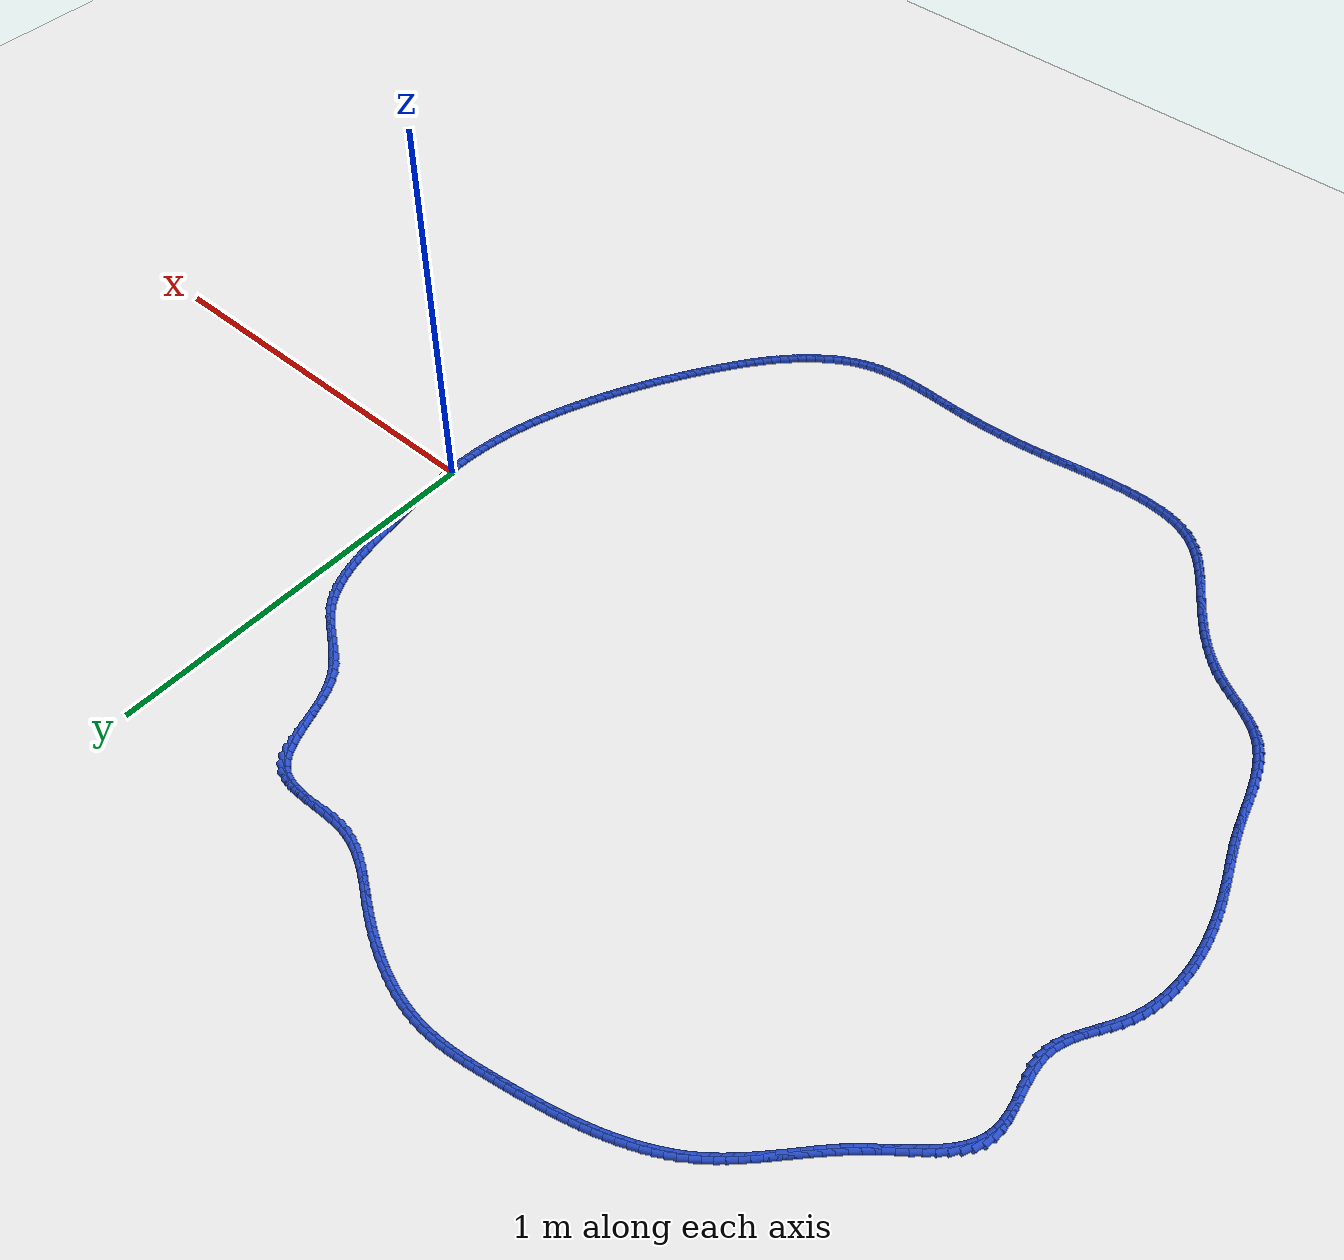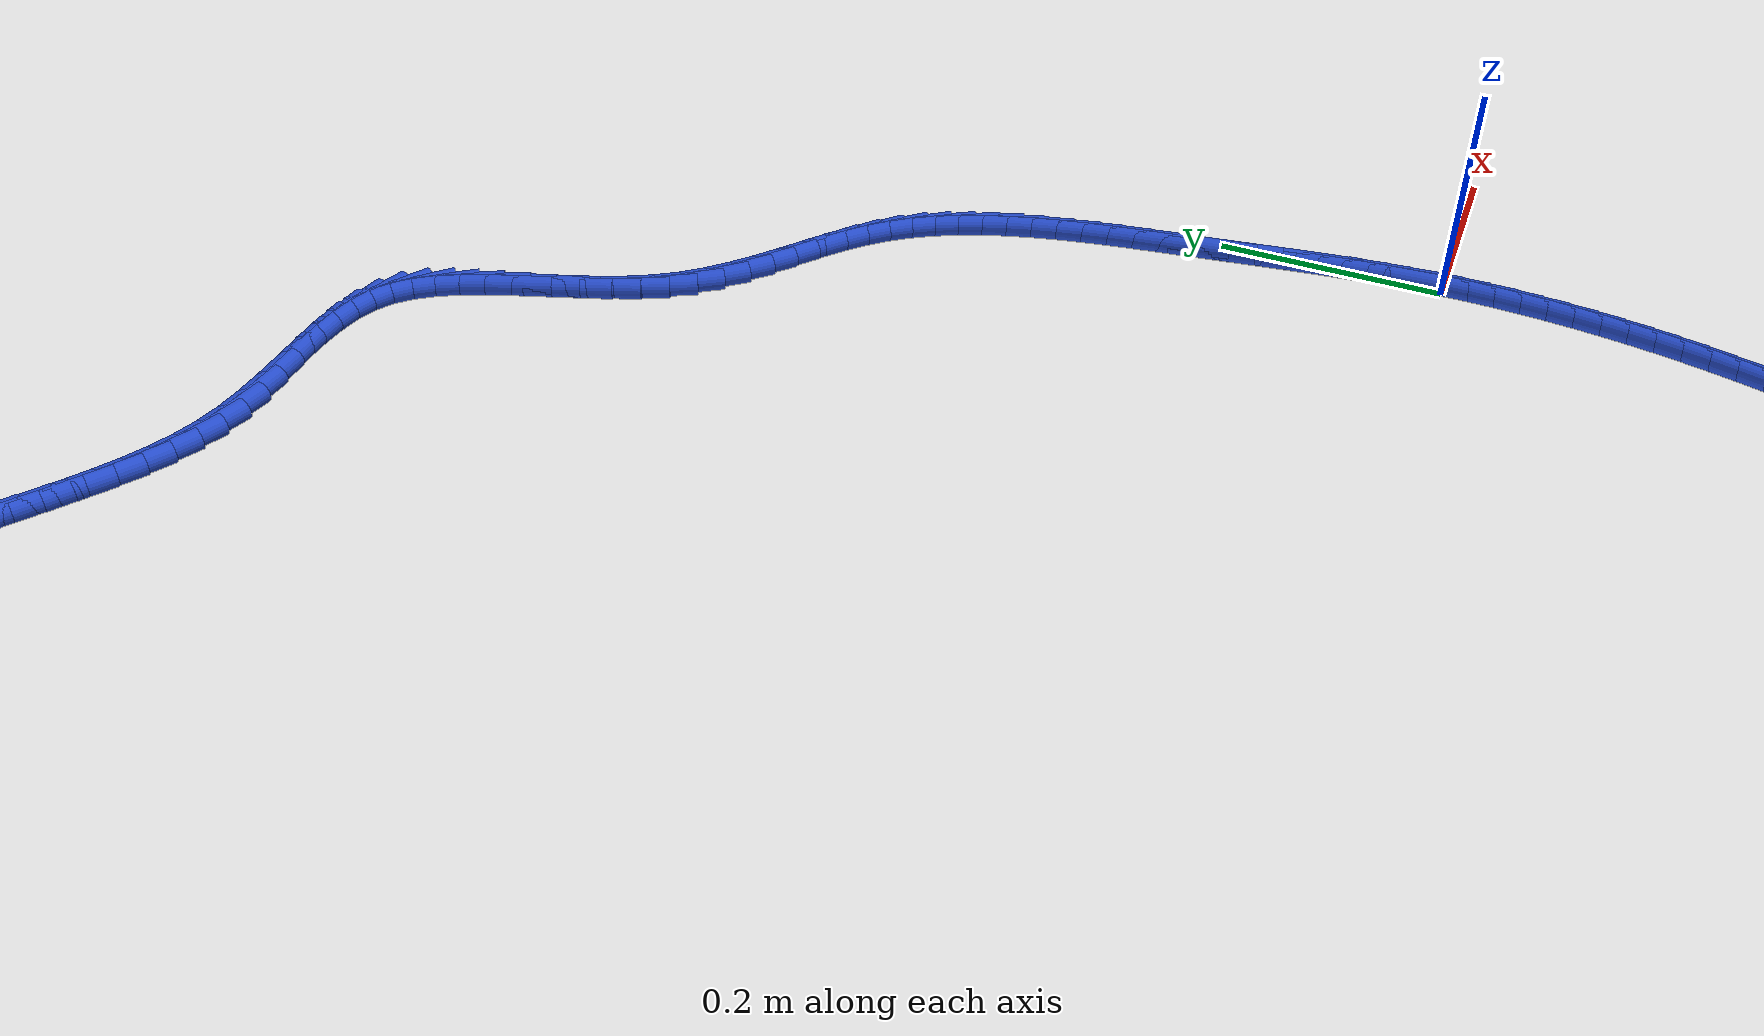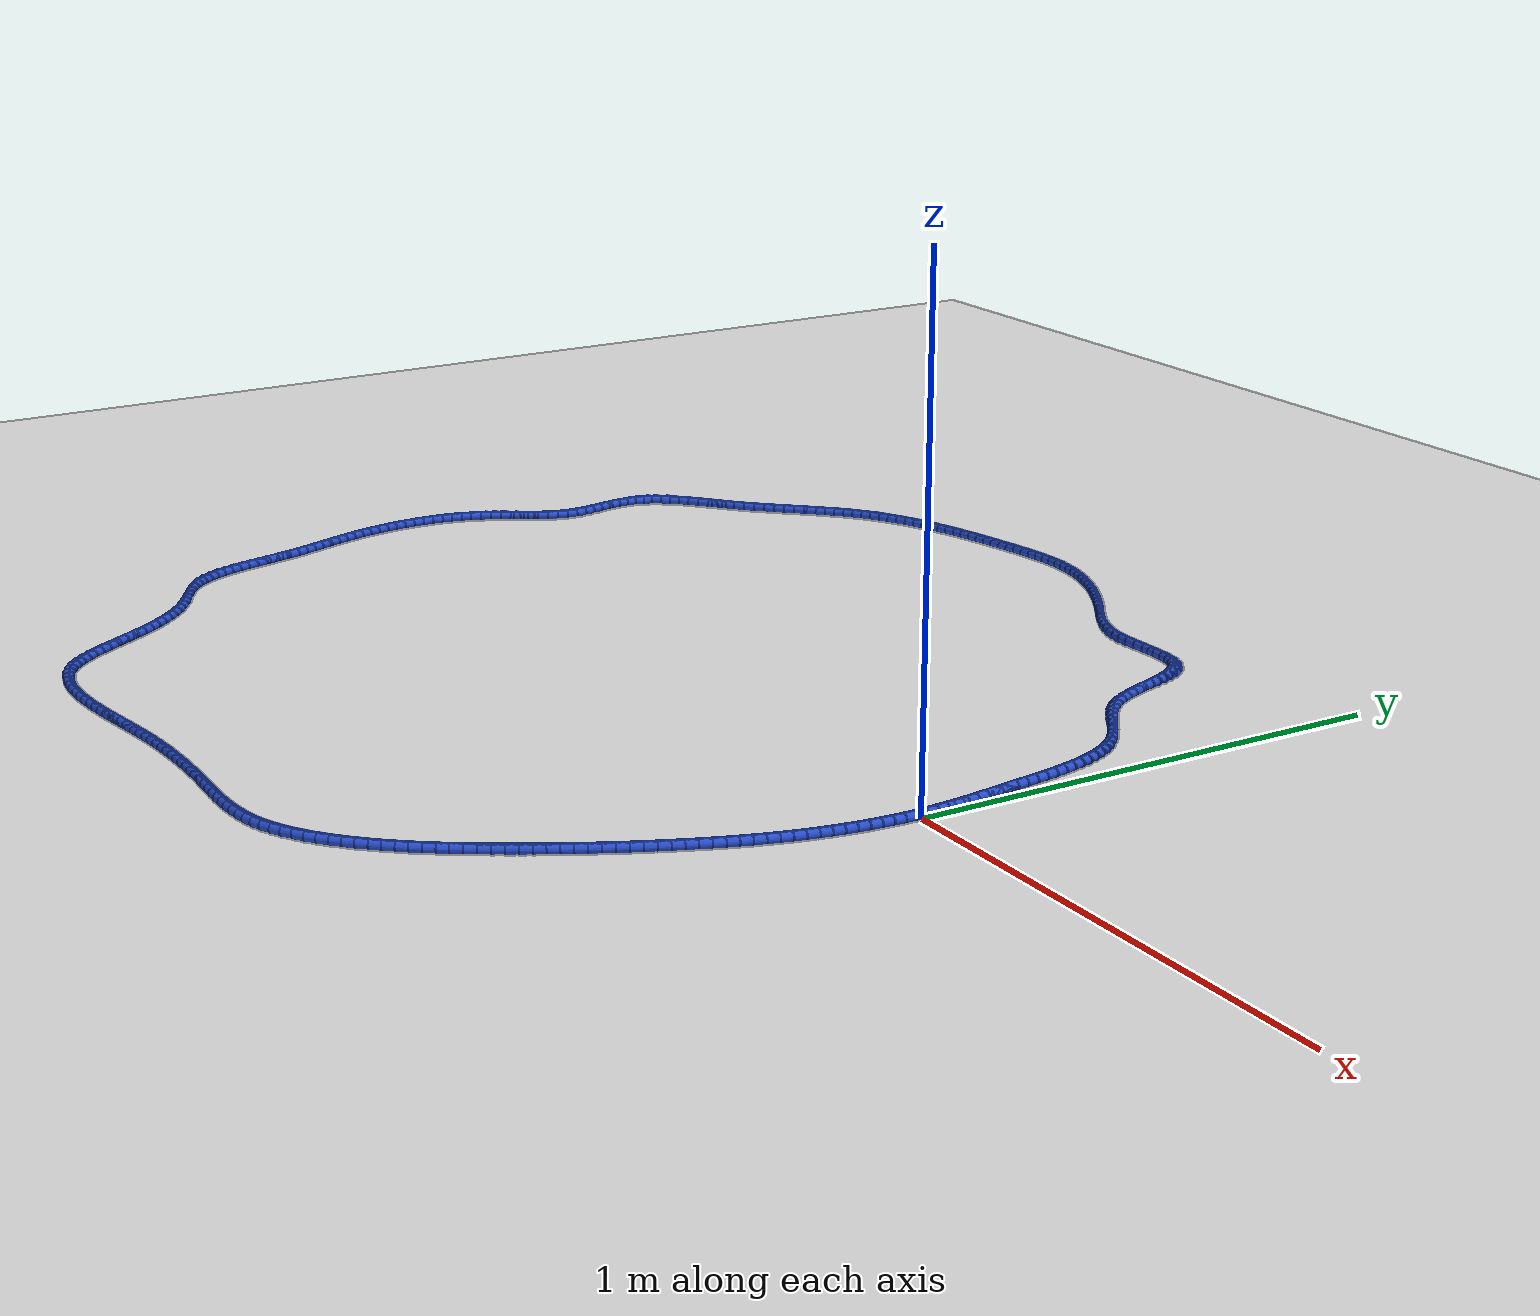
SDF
<sdf version="1.6">
 <world name="default">
  <light name="sun" type="directional">
   <pose>0 0 10 0 -0 0</pose>
   <diffuse>0.8 0.8 0.8 1</diffuse>
   <specular>0.2 0.2 0.2 1</specular>
   <attenuation>
    <range>1000</range>
    <constant>0.9</constant>
    <linear>0.01</linear>
    <quadratic>0.001</quadratic>
   </attenuation>
   <direction>-0.5 0.1 -0.9</direction>
  </light>
  <model name="ground_plane">
   <static>1</static>
   <link name="link">
    <collision name="collision">
     <geometry><plane><normal>0 0 1</normal><size>100 100</size></plane></geometry>
     <surface><friction><ode><mu>100</mu><mu2>50</mu2></ode></friction></surface>
    </collision>
    <visual name="visual">
     <cast_shadows>0</cast_shadows>
     <geometry><plane><normal>0 0 1</normal><size>100 100</size></plane></geometry>
     <material>
      <script><uri>file://media/materials/scripts/gazebo.material</uri><name>Gazebo/WhiteGlow</name></script>
     </material>
    </visual>
   </link>
  </model>
  <gravity>0 0 -9.8</gravity>
  <magnetic_field>6e-06 2.3e-05 -4.2e-05</magnetic_field>
  <atmosphere type="adiabatic"/>
  <physics name="default_physics" default="0" type="ode">
   <max_step_size>0.001</max_step_size>
   <real_time_factor>1</real_time_factor>
   <real_time_update_rate>1000</real_time_update_rate>
  </physics>
  <scene><ambient>0.4 0.4 0.4 1</ambient><background>0.7 0.7 0.7 1</background><shadows>1</shadows></scene>
  <spherical_coordinates>
   <surface_model>EARTH_WGS84</surface_model>
   <latitude_deg>0</latitude_deg>
   <longitude_deg>0</longitude_deg>
   <elevation>0</elevation>
   <heading_deg>0</heading_deg>
  </spherical_coordinates>
  <model name="line">
   <link name="link_0">
    <pose>-8.673617379884035e-19 4.85722573273506e-17 0.01 0 1.57 -1.5356665718949125</pose>
    <collision name="collision">
     <geometry><cylinder><radius>0.01</radius><length>0.08</length></cylinder></geometry>
    </collision>
    <visual name="visual">
     <material>
      <script><name>Gazebo/Blue</name><uri>file://media/materials/scripts/gazebo.material</uri></script>
     </material>
     <geometry><cylinder><radius>0.01</radius><length>0.08</length></cylinder></geometry>
    </visual>
   </link>
   <link name="link_1">
    <pose>-0.0007996154583783103 0.022752407425781863 0.01 0 1.57 -1.5092630340679354</pose>
    <collision name="collision">
     <geometry><cylinder><radius>0.01</radius><length>0.08</length></cylinder></geometry>
    </collision>
    <visual name="visual">
     <material>
      <script><name>Gazebo/Blue</name><uri>file://media/materials/scripts/gazebo.material</uri></script>
     </material>
     <geometry><cylinder><radius>0.01</radius><length>0.08</length></cylinder></geometry>
    </visual>
   </link>
   <link name="link_2">
    <pose>-0.002196849538418594 0.045430702415152874 0.01 0 1.57 -1.4864036266909855</pose>
    <collision name="collision">
     <geometry><cylinder><radius>0.01</radius><length>0.08</length></cylinder></geometry>
    </collision>
    <visual name="visual">
     <material>
      <script><name>Gazebo/Blue</name><uri>file://media/materials/scripts/gazebo.material</uri></script>
     </material>
     <geometry><cylinder><radius>0.01</radius><length>0.08</length></cylinder></geometry>
    </visual>
   </link>
   <link name="link_3">
    <pose>-0.00411280927286085 0.06807968746805257 0.01 0 1.57 -1.4672261902516774</pose>
    <collision name="collision">
     <geometry><cylinder><radius>0.01</radius><length>0.08</length></cylinder></geometry>
    </collision>
    <visual name="visual">
     <material>
      <script><name>Gazebo/Blue</name><uri>file://media/materials/scripts/gazebo.material</uri></script>
     </material>
     <geometry><cylinder><radius>0.01</radius><length>0.08</length></cylinder></geometry>
    </visual>
   </link>
   <link name="link_4">
    <pose>-0.0064686016944450675 0.09074416508442043 0.01 0 1.57 -1.4518116624976236</pose>
    <collision name="collision">
     <geometry><cylinder><radius>0.01</radius><length>0.08</length></cylinder></geometry>
    </collision>
    <visual name="visual">
     <material>
      <script><name>Gazebo/Blue</name><uri>file://media/materials/scripts/gazebo.material</uri></script>
     </material>
     <geometry><cylinder><radius>0.01</radius><length>0.08</length></cylinder></geometry>
    </visual>
   </link>
   <link name="link_5">
    <pose>-0.009185333835911245 0.11346893776419592 0.01 0 1.57 -1.440190740140251</pose>
    <collision name="collision">
     <geometry><cylinder><radius>0.01</radius><length>0.08</length></cylinder></geometry>
    </collision>
    <visual name="visual">
     <material>
      <script><name>Gazebo/Blue</name><uri>file://media/materials/scripts/gazebo.material</uri></script>
     </material>
     <geometry><cylinder><radius>0.01</radius><length>0.08</length></cylinder></geometry>
    </visual>
   </link>
   <link name="link_6">
    <pose>-0.012184112729999379 0.13629880800731858 0.01 0 1.57 -1.4323506813139588</pose>
    <collision name="collision">
     <geometry><cylinder><radius>0.01</radius><length>0.08</length></cylinder></geometry>
    </collision>
    <visual name="visual">
     <material>
      <script><name>Gazebo/Blue</name><uri>file://media/materials/scripts/gazebo.material</uri></script>
     </material>
     <geometry><cylinder><radius>0.01</radius><length>0.08</length></cylinder></geometry>
    </visual>
   </link>
   <link name="link_7">
    <pose>-0.01538604540944946 0.1592785783137279 0.01 0 1.57 -1.4282415661234653</pose>
    <collision name="collision">
     <geometry><cylinder><radius>0.01</radius><length>0.08</length></cylinder></geometry>
    </collision>
    <visual name="visual">
     <material>
      <script><name>Gazebo/Blue</name><uri>file://media/materials/scripts/gazebo.material</uri></script>
     </material>
     <geometry><cylinder><radius>0.01</radius><length>0.08</length></cylinder></geometry>
    </visual>
   </link>
   <link name="link_8">
    <pose>-0.018712238907001487 0.18245305118336336 0.01 0 1.57 -1.4277816055976553</pose>
    <collision name="collision">
     <geometry><cylinder><radius>0.01</radius><length>0.08</length></cylinder></geometry>
    </collision>
    <visual name="visual">
     <material>
      <script><name>Gazebo/Blue</name><uri>file://media/materials/scripts/gazebo.material</uri></script>
     </material>
     <geometry><cylinder><radius>0.01</radius><length>0.08</length></cylinder></geometry>
    </visual>
   </link>
   <link name="link_9">
    <pose>-0.022083800255395455 0.20586702911616445 0.01 0 1.57 -1.430461245277666</pose>
    <collision name="collision">
     <geometry><cylinder><radius>0.01</radius><length>0.08</length></cylinder></geometry>
    </collision>
    <visual name="visual">
     <material>
      <script><name>Gazebo/Blue</name><uri>file://media/materials/scripts/gazebo.material</uri></script>
     </material>
     <geometry><cylinder><radius>0.01</radius><length>0.08</length></cylinder></geometry>
    </visual>
   </link>
   <link name="link_10">
    <pose>-0.025430540108676923 0.22955847361248613 0.01 0 1.57 -1.4305754489350662</pose>
    <collision name="collision">
     <geometry><cylinder><radius>0.01</radius><length>0.08</length></cylinder></geometry>
    </collision>
    <visual name="visual">
     <material>
      <script><name>Gazebo/Blue</name><uri>file://media/materials/scripts/gazebo.material</uri></script>
     </material>
     <geometry><cylinder><radius>0.01</radius><length>0.08</length></cylinder></geometry>
    </visual>
   </link>
   <link name="link_11">
    <pose>-0.028805383698102312 0.25346857877644996 0.01 0 1.57 -1.4240507119331391</pose>
    <collision name="collision">
     <geometry><cylinder><radius>0.01</radius><length>0.08</length></cylinder></geometry>
    </collision>
    <visual name="visual">
     <material>
      <script><name>Gazebo/Blue</name><uri>file://media/materials/scripts/gazebo.material</uri></script>
     </material>
     <geometry><cylinder><radius>0.01</radius><length>0.08</length></cylinder></geometry>
    </visual>
   </link>
   <link name="link_12">
    <pose>-0.03235251692392895 0.27746680831665654 0.01 0 1.57 -1.4107939568309824</pose>
    <collision name="collision">
     <geometry><cylinder><radius>0.01</radius><length>0.08</length></cylinder></geometry>
    </collision>
    <visual name="visual">
     <material>
      <script><name>Gazebo/Blue</name><uri>file://media/materials/scripts/gazebo.material</uri></script>
     </material>
     <geometry><cylinder><radius>0.01</radius><length>0.08</length></cylinder></geometry>
    </visual>
   </link>
   <link name="link_13">
    <pose>-0.03621827897254508 0.30142093347037624 0.01 0 1.57 -1.3906377145496933</pose>
    <collision name="collision">
     <geometry><cylinder><radius>0.01</radius><length>0.08</length></cylinder></geometry>
    </collision>
    <visual name="visual">
     <material>
      <script><name>Gazebo/Blue</name><uri>file://media/materials/scripts/gazebo.material</uri></script>
     </material>
     <geometry><cylinder><radius>0.01</radius><length>0.08</length></cylinder></geometry>
    </visual>
   </link>
   <link name="link_14">
    <pose>-0.04054900903033896 0.3251987254748795 0.01 0 1.57 -1.3632533144146899</pose>
    <collision name="collision">
     <geometry><cylinder><radius>0.01</radius><length>0.08</length></cylinder></geometry>
    </collision>
    <visual name="visual">
     <material>
      <script><name>Gazebo/Blue</name><uri>file://media/materials/scripts/gazebo.material</uri></script>
     </material>
     <geometry><cylinder><radius>0.01</radius><length>0.08</length></cylinder></geometry>
    </visual>
   </link>
   <link name="link_15">
    <pose>-0.045491046283698815 0.3486679555674368 0.01 0 1.57 -1.3281660572148266</pose>
    <collision name="collision">
     <geometry><cylinder><radius>0.01</radius><length>0.08</length></cylinder></geometry>
    </collision>
    <visual name="visual">
     <material>
      <script><name>Gazebo/Blue</name><uri>file://media/materials/scripts/gazebo.material</uri></script>
     </material>
     <geometry><cylinder><radius>0.01</radius><length>0.08</length></cylinder></geometry>
    </visual>
   </link>
   <link name="link_16">
    <pose>-0.05119072991901294 0.37169639498531865 0.01 0 1.57 -1.2847803837345702</pose>
    <collision name="collision">
     <geometry><cylinder><radius>0.01</radius><length>0.08</length></cylinder></geometry>
    </collision>
    <visual name="visual">
     <material>
      <script><name>Gazebo/Blue</name><uri>file://media/materials/scripts/gazebo.material</uri></script>
     </material>
     <geometry><cylinder><radius>0.01</radius><length>0.08</length></cylinder></geometry>
    </visual>
   </link>
   <link name="link_17">
    <pose>-0.057794399122669565 0.39415181496579543 0.01 0 1.57 -1.2324254217158606</pose>
    <collision name="collision">
     <geometry><cylinder><radius>0.01</radius><length>0.08</length></cylinder></geometry>
    </collision>
    <visual name="visual">
     <material>
      <script><name>Gazebo/Blue</name><uri>file://media/materials/scripts/gazebo.material</uri></script>
     </material>
     <geometry><cylinder><radius>0.01</radius><length>0.08</length></cylinder></geometry>
    </visual>
   </link>
   <link name="link_18">
    <pose>-0.06544839308105695 0.4159019867461378 0.01 0 1.57 -1.1704348400482292</pose>
    <collision name="collision">
     <geometry><cylinder><radius>0.01</radius><length>0.08</length></cylinder></geometry>
    </collision>
    <visual name="visual">
     <material>
      <script><name>Gazebo/Blue</name><uri>file://media/materials/scripts/gazebo.material</uri></script>
     </material>
     <geometry><cylinder><radius>0.01</radius><length>0.08</length></cylinder></geometry>
    </visual>
   </link>
   <link name="link_19">
    <pose>-0.07429905098056333 0.4368146815636159 0.01 0 1.57 -1.0982764233818103</pose>
    <collision name="collision">
     <geometry><cylinder><radius>0.01</radius><length>0.08</length></cylinder></geometry>
    </collision>
    <visual name="visual">
     <material>
      <script><name>Gazebo/Blue</name><uri>file://media/materials/scripts/gazebo.material</uri></script>
     </material>
     <geometry><cylinder><radius>0.01</radius><length>0.08</length></cylinder></geometry>
    </visual>
   </link>
   <link name="link_20">
    <pose>-0.08449271200757699 0.45675767065550055 0.01 0 1.57 -1.0157411969104022</pose>
    <collision name="collision">
     <geometry><cylinder><radius>0.01</radius><length>0.08</length></cylinder></geometry>
    </collision>
    <visual name="visual">
     <material>
      <script><name>Gazebo/Blue</name><uri>file://media/materials/scripts/gazebo.material</uri></script>
     </material>
     <geometry><cylinder><radius>0.01</radius><length>0.08</length></cylinder></geometry>
    </visual>
   </link>
   <link name="link_21">
    <pose>-0.09617571534848621 0.47559872525906205 0.01 0 1.57 -0.9231817204876047</pose>
    <collision name="collision">
     <geometry><cylinder><radius>0.01</radius><length>0.08</length></cylinder></geometry>
    </collision>
    <visual name="visual">
     <material>
      <script><name>Gazebo/Blue</name><uri>file://media/materials/scripts/gazebo.material</uri></script>
     </material>
     <geometry><cylinder><radius>0.01</radius><length>0.08</length></cylinder></geometry>
    </visual>
   </link>
   <link name="link_22">
    <pose>-0.10949440018967913 0.4932056166115707 0.01 0 1.57 -0.8243447026275936</pose>
    <collision name="collision">
     <geometry><cylinder><radius>0.01</radius><length>0.08</length></cylinder></geometry>
    </collision>
    <visual name="visual">
     <material>
      <script><name>Gazebo/Blue</name><uri>file://media/materials/scripts/gazebo.material</uri></script>
     </material>
     <geometry><cylinder><radius>0.01</radius><length>0.08</length></cylinder></geometry>
    </visual>
   </link>
   <link name="link_23">
    <pose>-0.12455230791968612 0.5094846054683013 0.01 0 1.57 -0.7420834030354317</pose>
    <collision name="collision">
     <geometry><cylinder><radius>0.01</radius><length>0.08</length></cylinder></geometry>
    </collision>
    <visual name="visual">
     <material>
      <script><name>Gazebo/Blue</name><uri>file://media/materials/scripts/gazebo.material</uri></script>
     </material>
     <geometry><cylinder><radius>0.01</radius><length>0.08</length></cylinder></geometry>
    </visual>
   </link>
   <link name="link_24">
    <pose>-0.14110106268531142 0.5246584437520476 0.01 0 1.57 -0.6868104738537814</pose>
    <collision name="collision">
     <geometry><cylinder><radius>0.01</radius><length>0.08</length></cylinder></geometry>
    </collision>
    <visual name="visual">
     <material>
      <script><name>Gazebo/Blue</name><uri>file://media/materials/scripts/gazebo.material</uri></script>
     </material>
     <geometry><cylinder><radius>0.01</radius><length>0.08</length></cylinder></geometry>
    </visual>
   </link>
   <link name="link_25">
    <pose>-0.15871945764540837 0.5391053161825077 0.01 0 1.57 -0.6573678868618982</pose>
    <collision name="collision">
     <geometry><cylinder><radius>0.01</radius><length>0.08</length></cylinder></geometry>
    </collision>
    <visual name="visual">
     <material>
      <script><name>Gazebo/Blue</name><uri>file://media/materials/scripts/gazebo.material</uri></script>
     </material>
     <geometry><cylinder><radius>0.01</radius><length>0.08</length></cylinder></geometry>
    </visual>
   </link>
   <link name="link_26">
    <pose>-0.17698508938257662 0.5532044836011789 0.01 0 1.57 -0.6525379172176473</pose>
    <collision name="collision">
     <geometry><cylinder><radius>0.01</radius><length>0.08</length></cylinder></geometry>
    </collision>
    <visual name="visual">
     <material>
      <script><name>Gazebo/Blue</name><uri>file://media/materials/scripts/gazebo.material</uri></script>
     </material>
     <geometry><cylinder><radius>0.01</radius><length>0.08</length></cylinder></geometry>
    </visual>
   </link>
   <link name="link_27">
    <pose>-0.19547555447941573 0.5673352068495588 0.01 0 1.57 -0.6716407811316856</pose>
    <collision name="collision">
     <geometry><cylinder><radius>0.01</radius><length>0.08</length></cylinder></geometry>
    </collision>
    <visual name="visual">
     <material>
      <script><name>Gazebo/Blue</name><uri>file://media/materials/scripts/gazebo.material</uri></script>
     </material>
     <geometry><cylinder><radius>0.01</radius><length>0.08</length></cylinder></geometry>
    </visual>
   </link>
   <link name="link_28">
    <pose>-0.21376844951852572 0.5818767467691455 0.01 0 1.57 -0.7145779483354731</pose>
    <collision name="collision">
     <geometry><cylinder><radius>0.01</radius><length>0.08</length></cylinder></geometry>
    </collision>
    <visual name="visual">
     <material>
      <script><name>Gazebo/Blue</name><uri>file://media/materials/scripts/gazebo.material</uri></script>
     </material>
     <geometry><cylinder><radius>0.01</radius><length>0.08</length></cylinder></geometry>
    </visual>
   </link>
   <link name="link_29">
    <pose>-0.23144137108250606 0.5972083642014361 0.01 0 1.57 -0.7814868336258474</pose>
    <collision name="collision">
     <geometry><cylinder><radius>0.01</radius><length>0.08</length></cylinder></geometry>
    </collision>
    <visual name="visual">
     <material>
      <script><name>Gazebo/Blue</name><uri>file://media/materials/scripts/gazebo.material</uri></script>
     </material>
     <geometry><cylinder><radius>0.01</radius><length>0.08</length></cylinder></geometry>
    </visual>
   </link>
   <link name="link_30">
    <pose>-0.24807191575395637 0.6137093199879282 0.01 0 1.57 -0.8720020968075067</pose>
    <collision name="collision">
     <geometry><cylinder><radius>0.01</radius><length>0.08</length></cylinder></geometry>
    </collision>
    <visual name="visual">
     <material>
      <script><name>Gazebo/Blue</name><uri>file://media/materials/scripts/gazebo.material</uri></script>
     </material>
     <geometry><cylinder><radius>0.01</radius><length>0.08</length></cylinder></geometry>
    </visual>
   </link>
   <link name="link_31">
    <pose>-0.2632376801154765 0.6317588749701195 0.01 0 1.57 -0.9832125202567297</pose>
    <collision name="collision">
     <geometry><cylinder><radius>0.01</radius><length>0.08</length></cylinder></geometry>
    </collision>
    <visual name="visual">
     <material>
      <script><name>Gazebo/Blue</name><uri>file://media/materials/scripts/gazebo.material</uri></script>
     </material>
     <geometry><cylinder><radius>0.01</radius><length>0.08</length></cylinder></geometry>
    </visual>
   </link>
   <link name="link_32">
    <pose>-0.2765323002653723 0.6517189117487473 0.01 0 1.57 -1.0881716636845455</pose>
    <collision name="collision">
     <geometry><cylinder><radius>0.01</radius><length>0.08</length></cylinder></geometry>
    </collision>
    <visual name="visual">
     <material>
      <script><name>Gazebo/Blue</name><uri>file://media/materials/scripts/gazebo.material</uri></script>
     </material>
     <geometry><cylinder><radius>0.01</radius><length>0.08</length></cylinder></geometry>
    </visual>
   </link>
   <link name="link_33">
    <pose>-0.2879522916452171 0.673514807586541 0.01 0 1.57 -1.1635313918204884</pose>
    <collision name="collision">
     <geometry><cylinder><radius>0.01</radius><length>0.08</length></cylinder></geometry>
    </collision>
    <visual name="visual">
     <material>
      <script><name>Gazebo/Blue</name><uri>file://media/materials/scripts/gazebo.material</uri></script>
     </material>
     <geometry><cylinder><radius>0.01</radius><length>0.08</length></cylinder></geometry>
    </visual>
   </link>
   <link name="link_34">
    <pose>-0.2979168771394939 0.696613951372469 0.01 0 1.57 -1.2118281838493508</pose>
    <collision name="collision">
     <geometry><cylinder><radius>0.01</radius><length>0.08</length></cylinder></geometry>
    </collision>
    <visual name="visual">
     <material>
      <script><name>Gazebo/Blue</name><uri>file://media/materials/scripts/gazebo.material</uri></script>
     </material>
     <geometry><cylinder><radius>0.01</radius><length>0.08</length></cylinder></geometry>
    </visual>
   </link>
   <link name="link_35">
    <pose>-0.3068652876379082 0.7204620540384924 0.01 0 1.57 -1.2357343900301756</pose>
    <collision name="collision">
     <geometry><cylinder><radius>0.01</radius><length>0.08</length></cylinder></geometry>
    </collision>
    <visual name="visual">
     <material>
      <script><name>Gazebo/Blue</name><uri>file://media/materials/scripts/gazebo.material</uri></script>
     </material>
     <geometry><cylinder><radius>0.01</radius><length>0.08</length></cylinder></geometry>
    </visual>
   </link>
   <link name="link_36">
    <pose>-0.3152367540301653 0.7445048265165728 0.01 0 1.57 -1.2362050926118568</pose>
    <collision name="collision">
     <geometry><cylinder><radius>0.01</radius><length>0.08</length></cylinder></geometry>
    </collision>
    <visual name="visual">
     <material>
      <script><name>Gazebo/Blue</name><uri>file://media/materials/scripts/gazebo.material</uri></script>
     </material>
     <geometry><cylinder><radius>0.01</radius><length>0.08</length></cylinder></geometry>
    </visual>
   </link>
   <link name="link_37">
    <pose>-0.3234705072059704 0.7681879797386707 0.01 0 1.57 -1.2121487212611668</pose>
    <collision name="collision">
     <geometry><cylinder><radius>0.01</radius><length>0.08</length></cylinder></geometry>
    </collision>
    <visual name="visual">
     <material>
      <script><name>Gazebo/Blue</name><uri>file://media/materials/scripts/gazebo.material</uri></script>
     </material>
     <geometry><cylinder><radius>0.01</radius><length>0.08</length></cylinder></geometry>
    </visual>
   </link>
   <link name="link_38">
    <pose>-0.3320057780550288 0.7909572246367476 0.01 0 1.57 -1.1600889613823067</pose>
    <collision name="collision">
     <geometry><cylinder><radius>0.01</radius><length>0.08</length></cylinder></geometry>
    </collision>
    <visual name="visual">
     <material>
      <script><name>Gazebo/Blue</name><uri>file://media/materials/scripts/gazebo.material</uri></script>
     </material>
     <geometry><cylinder><radius>0.01</radius><length>0.08</length></cylinder></geometry>
    </visual>
   </link>
   <link name="link_39">
    <pose>-0.3412817974670458 0.8122582721427647 0.01 0 1.57 -1.0738345291637859</pose>
    <collision name="collision">
     <geometry><cylinder><radius>0.01</radius><length>0.08</length></cylinder></geometry>
    </collision>
    <visual name="visual">
     <material>
      <script><name>Gazebo/Blue</name><uri>file://media/materials/scripts/gazebo.material</uri></script>
     </material>
     <geometry><cylinder><radius>0.01</radius><length>0.08</length></cylinder></geometry>
    </visual>
   </link>
   <link name="link_40">
    <pose>-0.35173779633172675 0.8315368331886831 0.01 0 1.57 -0.9448074644204885</pose>
    <collision name="collision">
     <geometry><cylinder><radius>0.01</radius><length>0.08</length></cylinder></geometry>
    </collision>
    <visual name="visual">
     <material>
      <script><name>Gazebo/Blue</name><uri>file://media/materials/scripts/gazebo.material</uri></script>
     </material>
     <geometry><cylinder><radius>0.01</radius><length>0.08</length></cylinder></geometry>
    </visual>
   </link>
   <link name="link_41">
    <pose>-0.3638130055387768 0.8482386187064637 0.01 0 1.57 -0.7650818004135495</pose>
    <collision name="collision">
     <geometry><cylinder><radius>0.01</radius><length>0.08</length></cylinder></geometry>
    </collision>
    <visual name="visual">
     <material>
      <script><name>Gazebo/Blue</name><uri>file://media/materials/scripts/gazebo.material</uri></script>
     </material>
     <geometry><cylinder><radius>0.01</radius><length>0.08</length></cylinder></geometry>
    </visual>
   </link>
   <link name="link_42">
    <pose>-0.37794665597790156 0.8618093396280683 0.01 0 1.57 -0.5375890672606776</pose>
    <collision name="collision">
     <geometry><cylinder><radius>0.01</radius><length>0.08</length></cylinder></geometry>
    </collision>
    <visual name="visual">
     <material>
      <script><name>Gazebo/Blue</name><uri>file://media/materials/scripts/gazebo.material</uri></script>
     </material>
     <geometry><cylinder><radius>0.01</radius><length>0.08</length></cylinder></geometry>
    </visual>
   </link>
   <link name="link_43">
    <pose>-0.39456369777900524 0.8717157075281345 0.01 0 1.57 -0.3182826824693751</pose>
    <collision name="collision">
     <geometry><cylinder><radius>0.01</radius><length>0.08</length></cylinder></geometry>
    </collision>
    <visual name="visual">
     <material>
      <script><name>Gazebo/Blue</name><uri>file://media/materials/scripts/gazebo.material</uri></script>
     </material>
     <geometry><cylinder><radius>0.01</radius><length>0.08</length></cylinder></geometry>
    </visual>
   </link>
   <link name="link_44">
    <pose>-0.4136865420439354 0.8780163897602654 0.01 0 1.57 -0.15961761285592488</pose>
    <collision name="collision">
     <geometry><cylinder><radius>0.01</radius><length>0.08</length></cylinder></geometry>
    </collision>
    <visual name="visual">
     <material>
      <script><name>Gazebo/Blue</name><uri>file://media/materials/scripts/gazebo.material</uri></script>
     </material>
     <geometry><cylinder><radius>0.01</radius><length>0.08</length></cylinder></geometry>
    </visual>
   </link>
   <link name="link_45">
    <pose>-0.43488901940216934 0.8814297159330017 0.01 0 1.57 -0.05595362354177722</pose>
    <collision name="collision">
     <geometry><cylinder><radius>0.01</radius><length>0.08</length></cylinder></geometry>
    </collision>
    <visual name="visual">
     <material>
      <script><name>Gazebo/Blue</name><uri>file://media/materials/scripts/gazebo.material</uri></script>
     </material>
     <geometry><cylinder><radius>0.01</radius><length>0.08</length></cylinder></geometry>
    </visual>
   </link>
   <link name="link_46">
    <pose>-0.45772143756704936 0.8827086073967373 0.01 0 1.57 0.00427363072407046</pose>
    <collision name="collision">
     <geometry><cylinder><radius>0.01</radius><length>0.08</length></cylinder></geometry>
    </collision>
    <visual name="visual">
     <material>
      <script><name>Gazebo/Blue</name><uri>file://media/materials/scripts/gazebo.material</uri></script>
     </material>
     <geometry><cylinder><radius>0.01</radius><length>0.08</length></cylinder></geometry>
    </visual>
   </link>
   <link name="link_47">
    <pose>-0.48173410425191826 0.8826059855018659 0.01 0 1.57 0.029543489717894778</pose>
    <collision name="collision">
     <geometry><cylinder><radius>0.01</radius><length>0.08</length></cylinder></geometry>
    </collision>
    <visual name="visual">
     <material>
      <script><name>Gazebo/Blue</name><uri>file://media/materials/scripts/gazebo.material</uri></script>
     </material>
     <geometry><cylinder><radius>0.01</radius><length>0.08</length></cylinder></geometry>
    </visual>
   </link>
   <link name="link_48">
    <pose>-0.5064773271701184 0.8818747715987816 0.01 0 1.57 0.024247263220846523</pose>
    <collision name="collision">
     <geometry><cylinder><radius>0.01</radius><length>0.08</length></cylinder></geometry>
    </collision>
    <visual name="visual">
     <material>
      <script><name>Gazebo/Blue</name><uri>file://media/materials/scripts/gazebo.material</uri></script>
     </material>
     <geometry><cylinder><radius>0.01</radius><length>0.08</length></cylinder></geometry>
    </visual>
   </link>
   <link name="link_49">
    <pose>-0.5315014140349924 0.8812678870378782 0.01 0 1.57 -0.01087719400204119</pose>
    <collision name="collision">
     <geometry><cylinder><radius>0.01</radius><length>0.08</length></cylinder></geometry>
    </collision>
    <visual name="visual">
     <material>
      <script><name>Gazebo/Blue</name><uri>file://media/materials/scripts/gazebo.material</uri></script>
     </material>
     <geometry><cylinder><radius>0.01</radius><length>0.08</length></cylinder></geometry>
    </visual>
   </link>
   <link name="link_50">
    <pose>-0.5563566725598825 0.8815382531695493 0.01 0 1.57 -0.07825545742557245</pose>
    <collision name="collision">
     <geometry><cylinder><radius>0.01</radius><length>0.08</length></cylinder></geometry>
    </collision>
    <visual name="visual">
     <material>
      <script><name>Gazebo/Blue</name><uri>file://media/materials/scripts/gazebo.material</uri></script>
     </material>
     <geometry><cylinder><radius>0.01</radius><length>0.08</length></cylinder></geometry>
    </visual>
   </link>
   <link name="link_51">
    <pose>-0.5805934104581311 0.8834387913441889 0.01 0 1.57 -0.1804151709257667</pose>
    <collision name="collision">
     <geometry><cylinder><radius>0.01</radius><length>0.08</length></cylinder></geometry>
    </collision>
    <visual name="visual">
     <material>
      <script><name>Gazebo/Blue</name><uri>file://media/materials/scripts/gazebo.material</uri></script>
     </material>
     <geometry><cylinder><radius>0.01</radius><length>0.08</length></cylinder></geometry>
    </visual>
   </link>
   <link name="link_52">
    <pose>-0.6037916870424657 0.8876701217298072 0.01 0 1.57 -0.29135477854531094</pose>
    <collision name="collision">
     <geometry><cylinder><radius>0.01</radius><length>0.08</length></cylinder></geometry>
    </collision>
    <visual name="visual">
     <material>
      <script><name>Gazebo/Blue</name><uri>file://media/materials/scripts/gazebo.material</uri></script>
     </material>
     <geometry><cylinder><radius>0.01</radius><length>0.08</length></cylinder></geometry>
    </visual>
   </link>
   <link name="link_53">
    <pose>-0.6258927199051869 0.8942979740871754 0.01 0 1.57 -0.38834163661386867</pose>
    <collision name="collision">
     <geometry><cylinder><radius>0.01</radius><length>0.08</length></cylinder></geometry>
    </collision>
    <visual name="visual">
     <material>
      <script><name>Gazebo/Blue</name><uri>file://media/materials/scripts/gazebo.material</uri></script>
     </material>
     <geometry><cylinder><radius>0.01</radius><length>0.08</length></cylinder></geometry>
    </visual>
   </link>
   <link name="link_54">
    <pose>-0.6470782069305792 0.902965331035034 0.01 0 1.57 -0.4681032326094543</pose>
    <collision name="collision">
     <geometry><cylinder><radius>0.01</radius><length>0.08</length></cylinder></geometry>
    </collision>
    <visual name="visual">
     <material>
      <script><name>Gazebo/Blue</name><uri>file://media/materials/scripts/gazebo.material</uri></script>
     </material>
     <geometry><cylinder><radius>0.01</radius><length>0.08</length></cylinder></geometry>
    </visual>
   </link>
   <link name="link_55">
    <pose>-0.6675342036274943 0.9133075148000129 0.01 0 1.57 -0.5294474183096988</pose>
    <collision name="collision">
     <geometry><cylinder><radius>0.01</radius><length>0.08</length></cylinder></geometry>
    </collision>
    <visual name="visual">
     <material>
      <script><name>Gazebo/Blue</name><uri>file://media/materials/scripts/gazebo.material</uri></script>
     </material>
     <geometry><cylinder><radius>0.01</radius><length>0.08</length></cylinder></geometry>
    </visual>
   </link>
   <link name="link_56">
    <pose>-0.6874467655047829 0.9249598476087415 0.01 0 1.57 -0.5722999264462207</pose>
    <collision name="collision">
     <geometry><cylinder><radius>0.01</radius><length>0.08</length></cylinder></geometry>
    </collision>
    <visual name="visual">
     <material>
      <script><name>Gazebo/Blue</name><uri>file://media/materials/scripts/gazebo.material</uri></script>
     </material>
     <geometry><cylinder><radius>0.01</radius><length>0.08</length></cylinder></geometry>
    </visual>
   </link>
   <link name="link_57">
    <pose>-0.7070019480712963 0.9375576516878492 0.01 0 1.57 -0.5970910571866964</pose>
    <collision name="collision">
     <geometry><cylinder><radius>0.01</radius><length>0.08</length></cylinder></geometry>
    </collision>
    <visual name="visual">
     <material>
      <script><name>Gazebo/Blue</name><uri>file://media/materials/scripts/gazebo.material</uri></script>
     </material>
     <geometry><cylinder><radius>0.01</radius><length>0.08</length></cylinder></geometry>
    </visual>
   </link>
   <link name="link_58">
    <pose>-0.7263858068358859 0.9507362492639659 0.01 0 1.57 -0.6043211610480936</pose>
    <collision name="collision">
     <geometry><cylinder><radius>0.01</radius><length>0.08</length></cylinder></geometry>
    </collision>
    <visual name="visual">
     <material>
      <script><name>Gazebo/Blue</name><uri>file://media/materials/scripts/gazebo.material</uri></script>
     </material>
     <geometry><cylinder><radius>0.01</radius><length>0.08</length></cylinder></geometry>
    </visual>
   </link>
   <link name="link_59">
    <pose>-0.7457843973074021 0.9641309625637203 0.01 0 1.57 -0.5943682129795287</pose>
    <collision name="collision">
     <geometry><cylinder><radius>0.01</radius><length>0.08</length></cylinder></geometry>
    </collision>
    <visual name="visual">
     <material>
      <script><name>Gazebo/Blue</name><uri>file://media/materials/scripts/gazebo.material</uri></script>
     </material>
     <geometry><cylinder><radius>0.01</radius><length>0.08</length></cylinder></geometry>
    </visual>
   </link>
   <link name="link_60">
    <pose>-0.7653832554394021 0.9773778454273696 0.01 0 1.57 -0.5719724468831541</pose>
    <collision name="collision">
     <geometry><cylinder><radius>0.01</radius><length>0.08</length></cylinder></geometry>
    </collision>
    <visual name="visual">
     <material>
      <script><name>Gazebo/Blue</name><uri>file://media/materials/scripts/gazebo.material</uri></script>
     </material>
     <geometry><cylinder><radius>0.01</radius><length>0.08</length></cylinder></geometry>
    </visual>
   </link>
   <link name="link_61">
    <pose>-0.7853045043248059 0.9902022467391866 0.01 0 1.57 -0.5460568582457422</pose>
    <collision name="collision">
     <geometry><cylinder><radius>0.01</radius><length>0.08</length></cylinder></geometry>
    </collision>
    <visual name="visual">
     <material>
      <script><name>Gazebo/Blue</name><uri>file://media/materials/scripts/gazebo.material</uri></script>
     </material>
     <geometry><cylinder><radius>0.01</radius><length>0.08</length></cylinder></geometry>
    </visual>
   </link>
   <link name="link_62">
    <pose>-0.8055468147203727 1.002503355227305 0.01 0 1.57 -0.5175092670493209</pose>
    <collision name="collision">
     <geometry><cylinder><radius>0.01</radius><length>0.08</length></cylinder></geometry>
    </collision>
    <visual name="visual">
     <material>
      <script><name>Gazebo/Blue</name><uri>file://media/materials/scripts/gazebo.material</uri></script>
     </material>
     <geometry><cylinder><radius>0.01</radius><length>0.08</length></cylinder></geometry>
    </visual>
   </link>
   <link name="link_63">
    <pose>-0.826094632221733 1.0142003908308201 0.01 0 1.57 -0.48616508533799296</pose>
    <collision name="collision">
     <geometry><cylinder><radius>0.01</radius><length>0.08</length></cylinder></geometry>
    </collision>
    <visual name="visual">
     <material>
      <script><name>Gazebo/Blue</name><uri>file://media/materials/scripts/gazebo.material</uri></script>
     </material>
     <geometry><cylinder><radius>0.01</radius><length>0.08</length></cylinder></geometry>
    </visual>
   </link>
   <link name="link_64">
    <pose>-0.8469324024245178 1.0252125734888275 0.01 0 1.57 -0.4518498195295138</pose>
    <collision name="collision">
     <geometry><cylinder><radius>0.01</radius><length>0.08</length></cylinder></geometry>
    </collision>
    <visual name="visual">
     <material>
      <script><name>Gazebo/Blue</name><uri>file://media/materials/scripts/gazebo.material</uri></script>
     </material>
     <geometry><cylinder><radius>0.01</radius><length>0.08</length></cylinder></geometry>
    </visual>
   </link>
   <link name="link_65">
    <pose>-0.8680445709243582 1.0354591231404222 0.01 0 1.57 -0.41438499198066575</pose>
    <collision name="collision">
     <geometry><cylinder><radius>0.01</radius><length>0.08</length></cylinder></geometry>
    </collision>
    <visual name="visual">
     <material>
      <script><name>Gazebo/Blue</name><uri>file://media/materials/scripts/gazebo.material</uri></script>
     </material>
     <geometry><cylinder><radius>0.01</radius><length>0.08</length></cylinder></geometry>
    </visual>
   </link>
   <link name="link_66">
    <pose>-0.8894155833168846 1.0448592597247 0.01 0 1.57 -0.37359635693045407</pose>
    <collision name="collision">
     <geometry><cylinder><radius>0.01</radius><length>0.08</length></cylinder></geometry>
    </collision>
    <visual name="visual">
     <material>
      <script><name>Gazebo/Blue</name><uri>file://media/materials/scripts/gazebo.material</uri></script>
     </material>
     <geometry><cylinder><radius>0.01</radius><length>0.08</length></cylinder></geometry>
    </visual>
   </link>
   <link name="link_67">
    <pose>-0.9110298851977281 1.0533322031807562 0.01 0 1.57 -0.3293249491597048</pose>
    <collision name="collision">
     <geometry><cylinder><radius>0.01</radius><length>0.08</length></cylinder></geometry>
    </collision>
    <visual name="visual">
     <material>
      <script><name>Gazebo/Blue</name><uri>file://media/materials/scripts/gazebo.material</uri></script>
     </material>
     <geometry><cylinder><radius>0.01</radius><length>0.08</length></cylinder></geometry>
    </visual>
   </link>
   <link name="link_68">
    <pose>-0.9328719221625197 1.060797173447686 0.01 0 1.57 -0.28144138073006025</pose>
    <collision name="collision">
     <geometry><cylinder><radius>0.01</radius><length>0.08</length></cylinder></geometry>
    </collision>
    <visual name="visual">
     <material>
      <script><name>Gazebo/Blue</name><uri>file://media/materials/scripts/gazebo.material</uri></script>
     </material>
     <geometry><cylinder><radius>0.01</radius><length>0.08</length></cylinder></geometry>
    </visual>
   </link>
   <link name="link_69">
    <pose>-0.9549261398068898 1.0671733904645846 0.01 0 1.57 -0.2298634976252178</pose>
    <collision name="collision">
     <geometry><cylinder><radius>0.01</radius><length>0.08</length></cylinder></geometry>
    </collision>
    <visual name="visual">
     <material>
      <script><name>Gazebo/Blue</name><uri>file://media/materials/scripts/gazebo.material</uri></script>
     </material>
     <geometry><cylinder><radius>0.01</radius><length>0.08</length></cylinder></geometry>
    </visual>
   </link>
   <link name="link_70">
    <pose>-0.9771769837264694 1.072380074170548 0.01 0 1.57 -0.1745769533860519</pose>
    <collision name="collision">
     <geometry><cylinder><radius>0.01</radius><length>0.08</length></cylinder></geometry>
    </collision>
    <visual name="visual">
     <material>
      <script><name>Gazebo/Blue</name><uri>file://media/materials/scripts/gazebo.material</uri></script>
     </material>
     <geometry><cylinder><radius>0.01</radius><length>0.08</length></cylinder></geometry>
    </visual>
   </link>
   <link name="link_71">
    <pose>-0.9996088995168895 1.0763364445046708 0.01 0 1.57 -0.11567164917365573</pose>
    <collision name="collision">
     <geometry><cylinder><radius>0.01</radius><length>0.08</length></cylinder></geometry>
    </collision>
    <visual name="visual">
     <material>
      <script><name>Gazebo/Blue</name><uri>file://media/materials/scripts/gazebo.material</uri></script>
     </material>
     <geometry><cylinder><radius>0.01</radius><length>0.08</length></cylinder></geometry>
    </visual>
   </link>
   <link name="link_72">
    <pose>-1.022206314070724 1.0789620452904838 0.01 0 1.57 -0.056189495473699544</pose>
    <collision name="collision">
     <geometry><cylinder><radius>0.01</radius><length>0.08</length></cylinder></geometry>
    </collision>
    <visual name="visual">
     <material>
      <script><name>Gazebo/Blue</name><uri>file://media/materials/scripts/gazebo.material</uri></script>
     </material>
     <geometry><cylinder><radius>0.01</radius><length>0.08</length></cylinder></geometry>
    </visual>
   </link>
   <link name="link_73">
    <pose>-1.0449499052608473 1.0802413428462674 0.01 0 1.57 -0.0026469788316476252</pose>
    <collision name="collision">
     <geometry><cylinder><radius>0.01</radius><length>0.08</length></cylinder></geometry>
    </collision>
    <visual name="visual">
     <material>
      <script><name>Gazebo/Blue</name><uri>file://media/materials/scripts/gazebo.material</uri></script>
     </material>
     <geometry><cylinder><radius>0.01</radius><length>0.08</length></cylinder></geometry>
    </visual>
   </link>
   <link name="link_74">
    <pose>-1.0678120900818837 1.0803018587068687 0.01 0 1.57 0.04404865448683342</pose>
    <collision name="collision">
     <geometry><cylinder><radius>0.01</radius><length>0.08</length></cylinder></geometry>
    </collision>
    <visual name="visual">
     <material>
      <script><name>Gazebo/Blue</name><uri>file://media/materials/scripts/gazebo.material</uri></script>
     </material>
     <geometry><cylinder><radius>0.01</radius><length>0.08</length></cylinder></geometry>
    </visual>
   </link>
   <link name="link_75">
    <pose>-1.0907641836714166 1.079290195477296 0.01 0 1.57 0.08398107908064396</pose>
    <collision name="collision">
     <geometry><cylinder><radius>0.01</radius><length>0.08</length></cylinder></geometry>
    </collision>
    <visual name="visual">
     <material>
      <script><name>Gazebo/Blue</name><uri>file://media/materials/scripts/gazebo.material</uri></script>
     </material>
     <geometry><cylinder><radius>0.01</radius><length>0.08</length></cylinder></geometry>
    </visual>
   </link>
   <link name="link_76">
    <pose>-1.1137775011670292 1.077352955762559 0.01 0 1.57 0.11732001219181902</pose>
    <collision name="collision">
     <geometry><cylinder><radius>0.01</radius><length>0.08</length></cylinder></geometry>
    </collision>
    <visual name="visual">
     <material>
      <script><name>Gazebo/Blue</name><uri>file://media/materials/scripts/gazebo.material</uri></script>
     </material>
     <geometry><cylinder><radius>0.01</radius><length>0.08</length></cylinder></geometry>
    </visual>
   </link>
   <link name="link_77">
    <pose>-1.1368233577063058 1.0746367421676657 0.01 0 1.57 0.14426736907130147</pose>
    <collision name="collision">
     <geometry><cylinder><radius>0.01</radius><length>0.08</length></cylinder></geometry>
    </collision>
    <visual name="visual">
     <material>
      <script><name>Gazebo/Blue</name><uri>file://media/materials/scripts/gazebo.material</uri></script>
     </material>
     <geometry><cylinder><radius>0.01</radius><length>0.08</length></cylinder></geometry>
    </visual>
   </link>
   <link name="link_78">
    <pose>-1.1598730684268292 1.0712881572976252 0.01 0 1.57 0.16501655797470746</pose>
    <collision name="collision">
     <geometry><cylinder><radius>0.01</radius><length>0.08</length></cylinder></geometry>
    </collision>
    <visual name="visual">
     <material>
      <script><name>Gazebo/Blue</name><uri>file://media/materials/scripts/gazebo.material</uri></script>
     </material>
     <geometry><cylinder><radius>0.01</radius><length>0.08</length></cylinder></geometry>
    </visual>
   </link>
   <link name="link_79">
    <pose>-1.1828979484661835 1.0674538037574464 0.01 0 1.57 0.1797231965092913</pose>
    <collision name="collision">
     <geometry><cylinder><radius>0.01</radius><length>0.08</length></cylinder></geometry>
    </collision>
    <visual name="visual">
     <material>
      <script><name>Gazebo/Blue</name><uri>file://media/materials/scripts/gazebo.material</uri></script>
     </material>
     <geometry><cylinder><radius>0.01</radius><length>0.08</length></cylinder></geometry>
    </visual>
   </link>
   <link name="link_80">
    <pose>-1.205869312961952 1.0632802841521385 0.01 0 1.57 0.18851031697392676</pose>
    <collision name="collision">
     <geometry><cylinder><radius>0.01</radius><length>0.08</length></cylinder></geometry>
    </collision>
    <visual name="visual">
     <material>
      <script><name>Gazebo/Blue</name><uri>file://media/materials/scripts/gazebo.material</uri></script>
     </material>
     <geometry><cylinder><radius>0.01</radius><length>0.08</length></cylinder></geometry>
    </visual>
   </link>
   <link name="link_81">
    <pose>-1.228758554845221 1.05891357765483 0.01 0 1.57 0.1941432162042487</pose>
    <collision name="collision">
     <geometry><cylinder><radius>0.01</radius><length>0.08</length></cylinder></geometry>
    </collision>
    <visual name="visual">
     <material>
      <script><name>Gazebo/Blue</name><uri>file://media/materials/scripts/gazebo.material</uri></script>
     </material>
     <geometry><cylinder><radius>0.01</radius><length>0.08</length></cylinder></geometry>
    </visual>
   </link>
   <link name="link_82">
    <pose>-1.2515453552079618 1.0544332426770289 0.01 0 1.57 0.20175461592208171</pose>
    <collision name="collision">
     <geometry><cylinder><radius>0.01</radius><length>0.08</length></cylinder></geometry>
    </collision>
    <visual name="visual">
     <material>
      <script><name>Gazebo/Blue</name><uri>file://media/materials/scripts/gazebo.material</uri></script>
     </material>
     <geometry><cylinder><radius>0.01</radius><length>0.08</length></cylinder></geometry>
    </visual>
   </link>
   <link name="link_83">
    <pose>-1.2742249198809479 1.0497944234218928 0.01 0 1.57 0.2119221431425157</pose>
    <collision name="collision">
     <geometry><cylinder><radius>0.01</radius><length>0.08</length></cylinder></geometry>
    </collision>
    <visual name="visual">
     <material>
      <script><name>Gazebo/Blue</name><uri>file://media/materials/scripts/gazebo.material</uri></script>
     </material>
     <geometry><cylinder><radius>0.01</radius><length>0.08</length></cylinder></geometry>
    </visual>
   </link>
   <link name="link_84">
    <pose>-1.2967941610555442 1.044938589434022 0.01 0 1.57 0.22465268294512614</pose>
    <collision name="collision">
     <geometry><cylinder><radius>0.01</radius><length>0.08</length></cylinder></geometry>
    </collision>
    <visual name="visual">
     <material>
      <script><name>Gazebo/Blue</name><uri>file://media/materials/scripts/gazebo.material</uri></script>
     </material>
     <geometry><cylinder><radius>0.01</radius><length>0.08</length></cylinder></geometry>
    </visual>
   </link>
   <link name="link_85">
    <pose>-1.3192499909231157 1.0398072102580165 0.01 0 1.57 0.23994287480410498</pose>
    <collision name="collision">
     <geometry><cylinder><radius>0.01</radius><length>0.08</length></cylinder></geometry>
    </collision>
    <visual name="visual">
     <material>
      <script><name>Gazebo/Blue</name><uri>file://media/materials/scripts/gazebo.material</uri></script>
     </material>
     <geometry><cylinder><radius>0.01</radius><length>0.08</length></cylinder></geometry>
    </visual>
   </link>
   <link name="link_86">
    <pose>-1.341589321675029 1.034341755438476 0.01 0 1.57 0.2577765476401392</pose>
    <collision name="collision">
     <geometry><cylinder><radius>0.01</radius><length>0.08</length></cylinder></geometry>
    </collision>
    <visual name="visual">
     <material>
      <script><name>Gazebo/Blue</name><uri>file://media/materials/scripts/gazebo.material</uri></script>
     </material>
     <geometry><cylinder><radius>0.01</radius><length>0.08</length></cylinder></geometry>
    </visual>
   </link>
   <link name="link_87">
    <pose>-1.3638090655026491 1.0284836945200002 0.01 0 1.57 0.2781217973391646</pose>
    <collision name="collision">
     <geometry><cylinder><radius>0.01</radius><length>0.08</length></cylinder></geometry>
    </collision>
    <visual name="visual">
     <material>
      <script><name>Gazebo/Blue</name><uri>file://media/materials/scripts/gazebo.material</uri></script>
     </material>
     <geometry><cylinder><radius>0.01</radius><length>0.08</length></cylinder></geometry>
    </visual>
   </link>
   <link name="link_88">
    <pose>-1.3859061345973411 1.02217449704719 0.01 0 1.57 0.30092783740872114</pose>
    <collision name="collision">
     <geometry><cylinder><radius>0.01</radius><length>0.08</length></cylinder></geometry>
    </collision>
    <visual name="visual">
     <material>
      <script><name>Gazebo/Blue</name><uri>file://media/materials/scripts/gazebo.material</uri></script>
     </material>
     <geometry><cylinder><radius>0.01</radius><length>0.08</length></cylinder></geometry>
    </visual>
   </link>
   <link name="link_89">
    <pose>-1.407877441150471 1.0153556325646447 0.01 0 1.57 0.32612180995729956</pose>
    <collision name="collision">
     <geometry><cylinder><radius>0.01</radius><length>0.08</length></cylinder></geometry>
    </collision>
    <visual name="visual">
     <material>
      <script><name>Gazebo/Blue</name><uri>file://media/materials/scripts/gazebo.material</uri></script>
     </material>
     <geometry><cylinder><radius>0.01</radius><length>0.08</length></cylinder></geometry>
    </visual>
   </link>
   <link name="link_90">
    <pose>-1.429719897353404 1.0079685706169648 0.01 0 1.57 0.35360577450195674</pose>
    <collision name="collision">
     <geometry><cylinder><radius>0.01</radius><length>0.08</length></cylinder></geometry>
    </collision>
    <visual name="visual">
     <material>
      <script><name>Gazebo/Blue</name><uri>file://media/materials/scripts/gazebo.material</uri></script>
     </material>
     <geometry><cylinder><radius>0.01</radius><length>0.08</length></cylinder></geometry>
    </visual>
   </link>
   <link name="link_91">
    <pose>-1.4514303895983203 0.9999547909659963 0.01 0 1.57 0.3832612312111733</pose>
    <collision name="collision">
     <geometry><cylinder><radius>0.01</radius><length>0.08</length></cylinder></geometry>
    </collision>
    <visual name="visual">
     <material>
      <script><name>Gazebo/Blue</name><uri>file://media/materials/scripts/gazebo.material</uri></script>
     </material>
     <geometry><cylinder><radius>0.01</radius><length>0.08</length></cylinder></geometry>
    </visual>
   </link>
   <link name="link_92">
    <pose>-1.472981872889754 0.9912652509169162 0.01 0 1.57 0.41515794365928205</pose>
    <collision name="collision">
     <geometry><cylinder><radius>0.01</radius><length>0.08</length></cylinder></geometry>
    </collision>
    <visual name="visual">
     <material>
      <script><name>Gazebo/Blue</name><uri>file://media/materials/scripts/gazebo.material</uri></script>
     </material>
     <geometry><cylinder><radius>0.01</radius><length>0.08</length></cylinder></geometry>
    </visual>
   </link>
   <link name="link_93">
    <pose>-1.494279053815596 0.981877936183593 0.01 0 1.57 0.44958623319120117</pose>
    <collision name="collision">
     <geometry><cylinder><radius>0.01</radius><length>0.08</length></cylinder></geometry>
    </collision>
    <visual name="visual">
     <material>
      <script><name>Gazebo/Blue</name><uri>file://media/materials/scripts/gazebo.material</uri></script>
     </material>
     <geometry><cylinder><radius>0.01</radius><length>0.08</length></cylinder></geometry>
    </visual>
   </link>
   <link name="link_94">
    <pose>-1.5152145524976237 0.9717756190809894 0.01 0 1.57 0.4868753736844972</pose>
    <collision name="collision">
     <geometry><cylinder><radius>0.01</radius><length>0.08</length></cylinder></geometry>
    </collision>
    <visual name="visual">
     <material>
      <script><name>Gazebo/Blue</name><uri>file://media/materials/scripts/gazebo.material</uri></script>
     </material>
     <geometry><cylinder><radius>0.01</radius><length>0.08</length></cylinder></geometry>
    </visual>
   </link>
   <link name="link_95">
    <pose>-1.5356809890576153 0.9609410719240671 0.01 0 1.57 0.527380497972606</pose>
    <collision name="collision">
     <geometry><cylinder><radius>0.01</radius><length>0.08</length></cylinder></geometry>
    </collision>
    <visual name="visual">
     <material>
      <script><name>Gazebo/Blue</name><uri>file://media/materials/scripts/gazebo.material</uri></script>
     </material>
     <geometry><cylinder><radius>0.01</radius><length>0.08</length></cylinder></geometry>
    </visual>
   </link>
   <link name="link_96">
    <pose>-1.5555709836173488 0.949357067027789 0.01 0 1.57 0.5714798595390188</pose>
    <collision name="collision">
     <geometry><cylinder><radius>0.01</radius><length>0.08</length></cylinder></geometry>
    </collision>
    <visual name="visual">
     <material>
      <script><name>Gazebo/Blue</name><uri>file://media/materials/scripts/gazebo.material</uri></script>
     </material>
     <geometry><cylinder><radius>0.01</radius><length>0.08</length></cylinder></geometry>
    </visual>
   </link>
   <link name="link_97">
    <pose>-1.5747771562986024 0.9370063767071173 0.01 0 1.57 0.6193110020784869</pose>
    <collision name="collision">
     <geometry><cylinder><radius>0.01</radius><length>0.08</length></cylinder></geometry>
    </collision>
    <visual name="visual">
     <material>
      <script><name>Gazebo/Blue</name><uri>file://media/materials/scripts/gazebo.material</uri></script>
     </material>
     <geometry><cylinder><radius>0.01</radius><length>0.08</length></cylinder></geometry>
    </visual>
   </link>
   <link name="link_98">
    <pose>-1.5931984253349256 0.9238744184186672 0.01 0 1.57 0.6663151772824806</pose>
    <collision name="collision">
     <geometry><cylinder><radius>0.01</radius><length>0.08</length></cylinder></geometry>
    </collision>
    <visual name="visual">
     <material>
      <script><name>Gazebo/Blue</name><uri>file://media/materials/scripts/gazebo.material</uri></script>
     </material>
     <geometry><cylinder><radius>0.01</radius><length>0.08</length></cylinder></geometry>
    </visual>
   </link>
   <link name="link_99">
    <pose>-1.6108499954914757 0.9099954487568195 0.01 0 1.57 0.7078738209341552</pose>
    <collision name="collision">
     <geometry><cylinder><radius>0.01</radius><length>0.08</length></cylinder></geometry>
    </collision>
    <visual name="visual">
     <material>
      <script><name>Gazebo/Blue</name><uri>file://media/materials/scripts/gazebo.material</uri></script>
     </material>
     <geometry><cylinder><radius>0.01</radius><length>0.08</length></cylinder></geometry>
    </visual>
   </link>
   <link name="link_100">
    <pose>-1.6278494030983213 0.8954467025123731 0.01 0 1.57 0.7433939958493837</pose>
    <collision name="collision">
     <geometry><cylinder><radius>0.01</radius><length>0.08</length></cylinder></geometry>
    </collision>
    <visual name="visual">
     <material>
      <script><name>Gazebo/Blue</name><uri>file://media/materials/scripts/gazebo.material</uri></script>
     </material>
     <geometry><cylinder><radius>0.01</radius><length>0.08</length></cylinder></geometry>
    </visual>
   </link>
   <link name="link_101">
    <pose>-1.6443176772975547 0.8803068814209697 0.01 0 1.57 0.7725962431589013</pose>
    <collision name="collision">
     <geometry><cylinder><radius>0.01</radius><length>0.08</length></cylinder></geometry>
    </collision>
    <visual name="visual">
     <material>
      <script><name>Gazebo/Blue</name><uri>file://media/materials/scripts/gazebo.material</uri></script>
     </material>
     <geometry><cylinder><radius>0.01</radius><length>0.08</length></cylinder></geometry>
    </visual>
   </link>
   <link name="link_102">
    <pose>-1.6603758472312684 0.864654687218249 0.01 0 1.57 0.7953419939166329</pose>
    <collision name="collision">
     <geometry><cylinder><radius>0.01</radius><length>0.08</length></cylinder></geometry>
    </collision>
    <visual name="visual">
     <material>
      <script><name>Gazebo/Blue</name><uri>file://media/materials/scripts/gazebo.material</uri></script>
     </material>
     <geometry><cylinder><radius>0.01</radius><length>0.08</length></cylinder></geometry>
    </visual>
   </link>
   <link name="link_103">
    <pose>-1.6761449420415562 0.8485688216398523 0.01 0 1.57 0.8116011850671496</pose>
    <collision name="collision">
     <geometry><cylinder><radius>0.01</radius><length>0.08</length></cylinder></geometry>
    </collision>
    <visual name="visual">
     <material>
      <script><name>Gazebo/Blue</name><uri>file://media/materials/scripts/gazebo.material</uri></script>
     </material>
     <geometry><cylinder><radius>0.01</radius><length>0.08</length></cylinder></geometry>
    </visual>
   </link>
   <link name="link_104">
    <pose>-1.6917459908705101 0.8321279864214202 0.01 0 1.57 0.8214231727578891</pose>
    <collision name="collision">
     <geometry><cylinder><radius>0.01</radius><length>0.08</length></cylinder></geometry>
    </collision>
    <visual name="visual">
     <material>
      <script><name>Gazebo/Blue</name><uri>file://media/materials/scripts/gazebo.material</uri></script>
     </material>
     <geometry><cylinder><radius>0.01</radius><length>0.08</length></cylinder></geometry>
    </visual>
   </link>
   <link name="link_105">
    <pose>-1.7073000228602222 0.8154108832985933 0.01 0 1.57 0.8249140825073089</pose>
    <collision name="collision">
     <geometry><cylinder><radius>0.01</radius><length>0.08</length></cylinder></geometry>
    </collision>
    <visual name="visual">
     <material>
      <script><name>Gazebo/Blue</name><uri>file://media/materials/scripts/gazebo.material</uri></script>
     </material>
     <geometry><cylinder><radius>0.01</radius><length>0.08</length></cylinder></geometry>
    </visual>
   </link>
   <link name="link_106">
    <pose>-1.7229280671527865 0.7984962140070128 0.01 0 1.57 0.8222218184924835</pose>
    <collision name="collision">
     <geometry><cylinder><radius>0.01</radius><length>0.08</length></cylinder></geometry>
    </collision>
    <visual name="visual">
     <material>
      <script><name>Gazebo/Blue</name><uri>file://media/materials/scripts/gazebo.material</uri></script>
     </material>
     <geometry><cylinder><radius>0.01</radius><length>0.08</length></cylinder></geometry>
    </visual>
   </link>
   <link name="link_107">
    <pose>-1.7387511528902946 0.7814626802823189 0.01 0 1.57 0.813528646006731</pose>
    <collision name="collision">
     <geometry><cylinder><radius>0.01</radius><length>0.08</length></cylinder></geometry>
    </collision>
    <visual name="visual">
     <material>
      <script><name>Gazebo/Blue</name><uri>file://media/materials/scripts/gazebo.material</uri></script>
     </material>
     <geometry><cylinder><radius>0.01</radius><length>0.08</length></cylinder></geometry>
    </visual>
   </link>
   <link name="link_108">
    <pose>-1.7548903092148398 0.7643889838601533 0.01 0 1.57 0.7990504550523471</pose>
    <collision name="collision">
     <geometry><cylinder><radius>0.01</radius><length>0.08</length></cylinder></geometry>
    </collision>
    <visual name="visual">
     <material>
      <script><name>Gazebo/Blue</name><uri>file://media/materials/scripts/gazebo.material</uri></script>
     </material>
     <geometry><cylinder><radius>0.01</radius><length>0.08</length></cylinder></geometry>
    </visual>
   </link>
   <link name="link_109">
    <pose>-1.771466565268514 0.7473538264761552 0.01 0 1.57 0.7790413126371049</pose>
    <collision name="collision">
     <geometry><cylinder><radius>0.01</radius><length>0.08</length></cylinder></geometry>
    </collision>
    <visual name="visual">
     <material>
      <script><name>Gazebo/Blue</name><uri>file://media/materials/scripts/gazebo.material</uri></script>
     </material>
     <geometry><cylinder><radius>0.01</radius><length>0.08</length></cylinder></geometry>
    </visual>
   </link>
   <link name="link_110">
    <pose>-1.788600950193411 0.7304359098659666 0.01 0 1.57 0.7538015448354323</pose>
    <collision name="collision">
     <geometry><cylinder><radius>0.01</radius><length>0.08</length></cylinder></geometry>
    </collision>
    <visual name="visual">
     <material>
      <script><name>Gazebo/Blue</name><uri>file://media/materials/scripts/gazebo.material</uri></script>
     </material>
     <geometry><cylinder><radius>0.01</radius><length>0.08</length></cylinder></geometry>
    </visual>
   </link>
   <link name="link_111">
    <pose>-1.8064144931316226 0.7137139357652277 0.01 0 1.57 0.7248236412766847</pose>
    <collision name="collision">
     <geometry><cylinder><radius>0.01</radius><length>0.08</length></cylinder></geometry>
    </collision>
    <visual name="visual">
     <material>
      <script><name>Gazebo/Blue</name><uri>file://media/materials/scripts/gazebo.material</uri></script>
     </material>
     <geometry><cylinder><radius>0.01</radius><length>0.08</length></cylinder></geometry>
    </visual>
   </link>
   <link name="link_112">
    <pose>-1.8249987922706286 0.6972549660007393 0.01 0 1.57 0.7043877822348676</pose>
    <collision name="collision">
     <geometry><cylinder><radius>0.01</radius><length>0.08</length></cylinder></geometry>
    </collision>
    <visual name="visual">
     <material>
      <script><name>Gazebo/Blue</name><uri>file://media/materials/scripts/gazebo.material</uri></script>
     </material>
     <geometry><cylinder><radius>0.01</radius><length>0.08</length></cylinder></geometry>
    </visual>
   </link>
   <link name="link_113">
    <pose>-1.8441264968978757 0.6809999184746548 0.01 0 1.57 0.6992294425343909</pose>
    <collision name="collision">
     <geometry><cylinder><radius>0.01</radius><length>0.08</length></cylinder></geometry>
    </collision>
    <visual name="visual">
     <material>
      <script><name>Gazebo/Blue</name><uri>file://media/materials/scripts/gazebo.material</uri></script>
     </material>
     <geometry><cylinder><radius>0.01</radius><length>0.08</length></cylinder></geometry>
    </visual>
   </link>
   <link name="link_114">
    <pose>-1.8633749828345685 0.6648124806568895 0.01 0 1.57 0.709225004221987</pose>
    <collision name="collision">
     <geometry><cylinder><radius>0.01</radius><length>0.08</length></cylinder></geometry>
    </collision>
    <visual name="visual">
     <material>
      <script><name>Gazebo/Blue</name><uri>file://media/materials/scripts/gazebo.material</uri></script>
     </material>
     <geometry><cylinder><radius>0.01</radius><length>0.08</length></cylinder></geometry>
    </visual>
   </link>
   <link name="link_115">
    <pose>-1.882318812153481 0.648555227183078 0.01 0 1.57 0.7349988497843716</pose>
    <collision name="collision">
     <geometry><cylinder><radius>0.01</radius><length>0.08</length></cylinder></geometry>
    </collision>
    <visual name="visual">
     <material>
      <script><name>Gazebo/Blue</name><uri>file://media/materials/scripts/gazebo.material</uri></script>
     </material>
     <geometry><cylinder><radius>0.01</radius><length>0.08</length></cylinder></geometry>
    </visual>
   </link>
   <link name="link_116">
    <pose>-1.9005325469273884 0.6320907326888545 0.01 0 1.57 0.7780448618520328</pose>
    <collision name="collision">
     <geometry><cylinder><radius>0.01</radius><length>0.08</length></cylinder></geometry>
    </collision>
    <visual name="visual">
     <material>
      <script><name>Gazebo/Blue</name><uri>file://media/materials/scripts/gazebo.material</uri></script>
     </material>
     <geometry><cylinder><radius>0.01</radius><length>0.08</length></cylinder></geometry>
    </visual>
   </link>
   <link name="link_117">
    <pose>-1.9175907492290645 0.6152815718098534 0.01 0 1.57 0.8407004173095257</pose>
    <collision name="collision">
     <geometry><cylinder><radius>0.01</radius><length>0.08</length></cylinder></geometry>
    </collision>
    <visual name="visual">
     <material>
      <script><name>Gazebo/Blue</name><uri>file://media/materials/scripts/gazebo.material</uri></script>
     </material>
     <geometry><cylinder><radius>0.01</radius><length>0.08</length></cylinder></geometry>
    </visual>
   </link>
   <link name="link_118">
    <pose>-1.9330679811312839 0.5979903191817085 0.01 0 1.57 0.9259478060596975</pose>
    <collision name="collision">
     <geometry><cylinder><radius>0.01</radius><length>0.08</length></cylinder></geometry>
    </collision>
    <visual name="visual">
     <material>
      <script><name>Gazebo/Blue</name><uri>file://media/materials/scripts/gazebo.material</uri></script>
     </material>
     <geometry><cylinder><radius>0.01</radius><length>0.08</length></cylinder></geometry>
    </visual>
   </link>
   <link name="link_119">
    <pose>-1.946538804706821 0.5800795494400545 0.01 0 1.57 1.036768316722575</pose>
    <collision name="collision">
     <geometry><cylinder><radius>0.01</radius><length>0.08</length></cylinder></geometry>
    </collision>
    <visual name="visual">
     <material>
      <script><name>Gazebo/Blue</name><uri>file://media/materials/scripts/gazebo.material</uri></script>
     </material>
     <geometry><cylinder><radius>0.01</radius><length>0.08</length></cylinder></geometry>
    </visual>
   </link>
   <link name="link_120">
    <pose>-1.9575777820284512 0.5614118372205255 0.01 0 1.57 1.1746632424410919</pose>
    <collision name="collision">
     <geometry><cylinder><radius>0.01</radius><length>0.08</length></cylinder></geometry>
    </collision>
    <visual name="visual">
     <material>
      <script><name>Gazebo/Blue</name><uri>file://media/materials/scripts/gazebo.material</uri></script>
     </material>
     <geometry><cylinder><radius>0.01</radius><length>0.08</length></cylinder></geometry>
    </visual>
   </link>
   <link name="link_121">
    <pose>-1.9657594751689478 0.5418497571587559 0.01 0 1.57 1.3371906927652175</pose>
    <collision name="collision">
     <geometry><cylinder><radius>0.01</radius><length>0.08</length></cylinder></geometry>
    </collision>
    <visual name="visual">
     <material>
      <script><name>Gazebo/Blue</name><uri>file://media/materials/scripts/gazebo.material</uri></script>
     </material>
     <geometry><cylinder><radius>0.01</radius><length>0.08</length></cylinder></geometry>
    </visual>
   </link>
   <link name="link_122">
    <pose>-1.9706596972994663 0.5212562534007614 0.01 0 1.57 1.5000370958665104</pose>
    <collision name="collision">
     <geometry><cylinder><radius>0.01</radius><length>0.08</length></cylinder></geometry>
    </collision>
    <visual name="visual">
     <material>
      <script><name>Gazebo/Blue</name><uri>file://media/materials/scripts/gazebo.material</uri></script>
     </material>
     <geometry><cylinder><radius>0.01</radius><length>0.08</length></cylinder></geometry>
    </visual>
   </link>
   <link name="link_123">
    <pose>-1.9721950007230418 0.49959490697972886 0.01 0 1.57 -1.5214820642111615</pose>
    <collision name="collision">
     <geometry><cylinder><radius>0.01</radius><length>0.08</length></cylinder></geometry>
    </collision>
    <visual name="visual">
     <material>
      <script><name>Gazebo/Blue</name><uri>file://media/materials/scripts/gazebo.material</uri></script>
     </material>
     <geometry><cylinder><radius>0.01</radius><length>0.08</length></cylinder></geometry>
    </visual>
   </link>
   <link name="link_124">
    <pose>-1.9710830988981793 0.47706592089933747 0.01 0 1.57 -1.445121849532125</pose>
    <collision name="collision">
     <geometry><cylinder><radius>0.01</radius><length>0.08</length></cylinder></geometry>
    </collision>
    <visual name="visual">
     <material>
      <script><name>Gazebo/Blue</name><uri>file://media/materials/scripts/gazebo.material</uri></script>
     </material>
     <geometry><cylinder><radius>0.01</radius><length>0.08</length></cylinder></geometry>
    </visual>
   </link>
   <link name="link_125">
    <pose>-1.9681567481552007 0.4539034759351955 0.01 0 1.57 -1.4064286538435493</pose>
    <collision name="collision">
     <geometry><cylinder><radius>0.01</radius><length>0.08</length></cylinder></geometry>
    </collision>
    <visual name="visual">
     <material>
      <script><name>Gazebo/Blue</name><uri>file://media/materials/scripts/gazebo.material</uri></script>
     </material>
     <geometry><cylinder><radius>0.01</radius><length>0.08</length></cylinder></geometry>
    </visual>
   </link>
   <link name="link_126">
    <pose>-1.964248704824428 0.43034175286291315 0.01 0 1.57 -1.4014469778879837</pose>
    <collision name="collision">
     <geometry><cylinder><radius>0.01</radius><length>0.08</length></cylinder></geometry>
    </collision>
    <visual name="visual">
     <material>
      <script><name>Gazebo/Blue</name><uri>file://media/materials/scripts/gazebo.material</uri></script>
     </material>
     <geometry><cylinder><radius>0.01</radius><length>0.08</length></cylinder></geometry>
    </visual>
   </link>
   <link name="link_127">
    <pose>-1.9601917252361822 0.4066149324580994 0.01 0 1.57 -1.4291692513413985</pose>
    <collision name="collision">
     <geometry><cylinder><radius>0.01</radius><length>0.08</length></cylinder></geometry>
    </collision>
    <visual name="visual">
     <material>
      <script><name>Gazebo/Blue</name><uri>file://media/materials/scripts/gazebo.material</uri></script>
     </material>
     <geometry><cylinder><radius>0.01</radius><length>0.08</length></cylinder></geometry>
    </visual>
   </link>
   <link name="link_128">
    <pose>-1.9568185657207873 0.382957195496364 0.01 0 1.57 -1.491467328468943</pose>
    <collision name="collision">
     <geometry><cylinder><radius>0.01</radius><length>0.08</length></cylinder></geometry>
    </collision>
    <visual name="visual">
     <material>
      <script><name>Gazebo/Blue</name><uri>file://media/materials/scripts/gazebo.material</uri></script>
     </material>
     <geometry><cylinder><radius>0.01</radius><length>0.08</length></cylinder></geometry>
    </visual>
   </link>
   <link name="link_129">
    <pose>-1.9549619826085638 0.35960272275331623 0.01 0 1.57 1.5492039859242983</pose>
    <collision name="collision">
     <geometry><cylinder><radius>0.01</radius><length>0.08</length></cylinder></geometry>
    </collision>
    <visual name="visual">
     <material>
      <script><name>Gazebo/Blue</name><uri>file://media/materials/scripts/gazebo.material</uri></script>
     </material>
     <geometry><cylinder><radius>0.01</radius><length>0.08</length></cylinder></geometry>
    </visual>
   </link>
   <link name="link_130">
    <pose>-1.9554547322298337 0.33678569500456557 0.01 0 1.57 1.4084623753906156</pose>
    <collision name="collision">
     <geometry><cylinder><radius>0.01</radius><length>0.08</length></cylinder></geometry>
    </collision>
    <visual name="visual">
     <material>
      <script><name>Gazebo/Blue</name><uri>file://media/materials/scripts/gazebo.material</uri></script>
     </material>
     <geometry><cylinder><radius>0.01</radius><length>0.08</length></cylinder></geometry>
    </visual>
   </link>
   <link name="link_131">
    <pose>-1.9590680543310888 0.3147229880232724 0.01 0 1.57 1.2673195715738828</pose>
    <collision name="collision">
     <geometry><cylinder><radius>0.01</radius><length>0.08</length></cylinder></geometry>
    </collision>
    <visual name="visual">
     <material>
      <script><name>Gazebo/Blue</name><uri>file://media/materials/scripts/gazebo.material</uri></script>
     </material>
     <geometry><cylinder><radius>0.01</radius><length>0.08</length></cylinder></geometry>
    </visual>
   </link>
   <link name="link_132">
    <pose>-1.9657457469651358 0.29339871302312864 0.01 0 1.57 1.1580958786090998</pose>
    <collision name="collision">
     <geometry><cylinder><radius>0.01</radius><length>0.08</length></cylinder></geometry>
    </collision>
    <visual name="visual">
     <material>
      <script><name>Gazebo/Blue</name><uri>file://media/materials/scripts/gazebo.material</uri></script>
     </material>
     <geometry><cylinder><radius>0.01</radius><length>0.08</length></cylinder></geometry>
    </visual>
   </link>
   <link name="link_133">
    <pose>-1.9748391019811637 0.27263030549128153 0.01 0 1.57 1.0820570206552478</pose>
    <collision name="collision">
     <geometry><cylinder><radius>0.01</radius><length>0.08</length></cylinder></geometry>
    </collision>
    <visual name="visual">
     <material>
      <script><name>Gazebo/Blue</name><uri>file://media/materials/scripts/gazebo.material</uri></script>
     </material>
     <geometry><cylinder><radius>0.01</radius><length>0.08</length></cylinder></geometry>
    </visual>
   </link>
   <link name="link_134">
    <pose>-1.9856865308493465 0.2522315775831436 0.01 0 1.57 1.0372880795987787</pose>
    <collision name="collision">
     <geometry><cylinder><radius>0.01</radius><length>0.08</length></cylinder></geometry>
    </collision>
    <visual name="visual">
     <material>
      <script><name>Gazebo/Blue</name><uri>file://media/materials/scripts/gazebo.material</uri></script>
     </material>
     <geometry><cylinder><radius>0.01</radius><length>0.08</length></cylinder></geometry>
    </visual>
   </link>
   <link name="link_135">
    <pose>-1.9976264450398604 0.23201634145412786 0.01 0 1.57 1.021692239177428</pose>
    <collision name="collision">
     <geometry><cylinder><radius>0.01</radius><length>0.08</length></cylinder></geometry>
    </collision>
    <visual name="visual">
     <material>
      <script><name>Gazebo/Blue</name><uri>file://media/materials/scripts/gazebo.material</uri></script>
     </material>
     <geometry><cylinder><radius>0.01</radius><length>0.08</length></cylinder></geometry>
    </visual>
   </link>
   <link name="link_136">
    <pose>-2.009997256022879 0.2117984092596475 0.01 0 1.57 1.0341314886987998</pose>
    <collision name="collision">
     <geometry><cylinder><radius>0.01</radius><length>0.08</length></cylinder></geometry>
    </collision>
    <visual name="visual">
     <material>
      <script><name>Gazebo/Blue</name><uri>file://media/materials/scripts/gazebo.material</uri></script>
     </material>
     <geometry><cylinder><radius>0.01</radius><length>0.08</length></cylinder></geometry>
    </visual>
   </link>
   <link name="link_137">
    <pose>-2.022137375268579 0.19139159315511559 0.01 0 1.57 1.0747090942664412</pose>
    <collision name="collision">
     <geometry><cylinder><radius>0.01</radius><length>0.08</length></cylinder></geometry>
    </collision>
    <visual name="visual">
     <material>
      <script><name>Gazebo/Blue</name><uri>file://media/materials/scripts/gazebo.material</uri></script>
     </material>
     <geometry><cylinder><radius>0.01</radius><length>0.08</length></cylinder></geometry>
    </visual>
   </link>
   <link name="link_138">
    <pose>-2.0333852142471343 0.170609705295945 0.01 0 1.57 1.1417381217211717</pose>
    <collision name="collision">
     <geometry><cylinder><radius>0.01</radius><length>0.08</length></cylinder></geometry>
    </collision>
    <visual name="visual">
     <material>
      <script><name>Gazebo/Blue</name><uri>file://media/materials/scripts/gazebo.material</uri></script>
     </material>
     <geometry><cylinder><radius>0.01</radius><length>0.08</length></cylinder></geometry>
    </visual>
   </link>
   <link name="link_139">
    <pose>-2.0431397012364876 0.1492875660913785 0.01 0 1.57 1.2151551380727048</pose>
    <collision name="collision">
     <geometry><cylinder><radius>0.01</radius><length>0.08</length></cylinder></geometry>
    </collision>
    <visual name="visual">
     <material>
      <script><name>Gazebo/Blue</name><uri>file://media/materials/scripts/gazebo.material</uri></script>
     </material>
     <geometry><cylinder><radius>0.01</radius><length>0.08</length></cylinder></geometry>
    </visual>
   </link>
   <link name="link_140">
    <pose>-2.0512619125548297 0.12742042945161142 0.01 0 1.57 1.2850464116411364</pose>
    <collision name="collision">
     <geometry><cylinder><radius>0.01</radius><length>0.08</length></cylinder></geometry>
    </collision>
    <visual name="visual">
     <material>
      <script><name>Gazebo/Blue</name><uri>file://media/materials/scripts/gazebo.material</uri></script>
     </material>
     <geometry><cylinder><radius>0.01</radius><length>0.08</length></cylinder></geometry>
    </visual>
   </link>
   <link name="link_141">
    <pose>-2.057826034497036 0.10507752986593565 0.01 0 1.57 1.3510377499080213</pose>
    <collision name="collision">
     <geometry><cylinder><radius>0.01</radius><length>0.08</length></cylinder></geometry>
    </collision>
    <visual name="visual">
     <material>
      <script><name>Gazebo/Blue</name><uri>file://media/materials/scripts/gazebo.material</uri></script>
     </material>
     <geometry><cylinder><radius>0.01</radius><length>0.08</length></cylinder></geometry>
    </visual>
   </link>
   <link name="link_142">
    <pose>-2.0629073934616318 0.08232849760768965 0.01 0 1.57 1.4129758913174826</pose>
    <collision name="collision">
     <geometry><cylinder><radius>0.01</radius><length>0.08</length></cylinder></geometry>
    </collision>
    <visual name="visual">
     <material>
      <script><name>Gazebo/Blue</name><uri>file://media/materials/scripts/gazebo.material</uri></script>
     </material>
     <geometry><cylinder><radius>0.01</radius><length>0.08</length></cylinder></geometry>
    </visual>
   </link>
   <link name="link_143">
    <pose>-2.066581315847148 0.059242962950211836 0.01 0 1.57 1.4708490614557397</pose>
    <collision name="collision">
     <geometry><cylinder><radius>0.01</radius><length>0.08</length></cylinder></geometry>
    </collision>
    <visual name="visual">
     <material>
      <script><name>Gazebo/Blue</name><uri>file://media/materials/scripts/gazebo.material</uri></script>
     </material>
     <geometry><cylinder><radius>0.01</radius><length>0.08</length></cylinder></geometry>
    </visual>
   </link>
   <link name="link_144">
    <pose>-2.0689231280521136 0.03589055616684031 0.01 0 1.57 1.524754806497009</pose>
    <collision name="collision">
     <geometry><cylinder><radius>0.01</radius><length>0.08</length></cylinder></geometry>
    </collision>
    <visual name="visual">
     <material>
      <script><name>Gazebo/Blue</name><uri>file://media/materials/scripts/gazebo.material</uri></script>
     </material>
     <geometry><cylinder><radius>0.01</radius><length>0.08</length></cylinder></geometry>
    </visual>
   </link>
   <link name="link_145">
    <pose>-2.070008156475057 0.012340907530913381 0.01 0 1.57 -1.5667237091632993</pose>
    <collision name="collision">
     <geometry><cylinder><radius>0.01</radius><length>0.08</length></cylinder></geometry>
    </collision>
    <visual name="visual">
     <material>
      <script><name>Gazebo/Blue</name><uri>file://media/materials/scripts/gazebo.material</uri></script>
     </material>
     <geometry><cylinder><radius>0.01</radius><length>0.08</length></cylinder></geometry>
    </visual>
   </link>
   <link name="link_146">
    <pose>-2.069911727514506 -0.011336352684230647 0.01 0 1.57 -1.5201740259745384</pose>
    <collision name="collision">
     <geometry><cylinder><radius>0.01</radius><length>0.08</length></cylinder></geometry>
    </collision>
    <visual name="visual">
     <material>
      <script><name>Gazebo/Blue</name><uri>file://media/materials/scripts/gazebo.material</uri></script>
     </material>
     <geometry><cylinder><radius>0.01</radius><length>0.08</length></cylinder></geometry>
    </visual>
   </link>
   <link name="link_147">
    <pose>-2.0687091675689917 -0.0350715942052536 0.01 0 1.57 -1.476931890890407</pose>
    <collision name="collision">
     <geometry><cylinder><radius>0.01</radius><length>0.08</length></cylinder></geometry>
    </collision>
    <visual name="visual">
     <material>
      <script><name>Gazebo/Blue</name><uri>file://media/materials/scripts/gazebo.material</uri></script>
     </material>
     <geometry><cylinder><radius>0.01</radius><length>0.08</length></cylinder></geometry>
    </visual>
   </link>
   <link name="link_148">
    <pose>-2.066475803037041 -0.058795186758817175 0.01 0 1.57 -1.4367268029445421</pose>
    <collision name="collision">
     <geometry><cylinder><radius>0.01</radius><length>0.08</length></cylinder></geometry>
    </collision>
    <visual name="visual">
     <material>
      <script><name>Gazebo/Blue</name><uri>file://media/materials/scripts/gazebo.material</uri></script>
     </material>
     <geometry><cylinder><radius>0.01</radius><length>0.08</length></cylinder></geometry>
    </visual>
   </link>
   <link name="link_149">
    <pose>-2.0632869603171833 -0.08243750007158315 0.01 0 1.57 -1.399285994150578</pose>
    <collision name="collision">
     <geometry><cylinder><radius>0.01</radius><length>0.08</length></cylinder></geometry>
    </collision>
    <visual name="visual">
     <material>
      <script><name>Gazebo/Blue</name><uri>file://media/materials/scripts/gazebo.material</uri></script>
     </material>
     <geometry><cylinder><radius>0.01</radius><length>0.08</length></cylinder></geometry>
    </visual>
   </link>
   <link name="link_150">
    <pose>-2.0592179658079477 -0.10592890387021327 0.01 0 1.57 -1.3643417691982271</pose>
    <collision name="collision">
     <geometry><cylinder><radius>0.01</radius><length>0.08</length></cylinder></geometry>
    </collision>
    <visual name="visual">
     <material>
      <script><name>Gazebo/Blue</name><uri>file://media/materials/scripts/gazebo.material</uri></script>
     </material>
     <geometry><cylinder><radius>0.01</radius><length>0.08</length></cylinder></geometry>
    </visual>
   </link>
   <link name="link_151">
    <pose>-2.0543441459078635 -0.12919976788136928 0.01 0 1.57 -1.331635716571427</pose>
    <collision name="collision">
     <geometry><cylinder><radius>0.01</radius><length>0.08</length></cylinder></geometry>
    </collision>
    <visual name="visual">
     <material>
      <script><name>Gazebo/Blue</name><uri>file://media/materials/scripts/gazebo.material</uri></script>
     </material>
     <geometry><cylinder><radius>0.01</radius><length>0.08</length></cylinder></geometry>
    </visual>
   </link>
   <link name="link_152">
    <pose>-2.0487408270154592 -0.1521804618317122 0.01 0 1.57 -1.300920537341398</pose>
    <collision name="collision">
     <geometry><cylinder><radius>0.01</radius><length>0.08</length></cylinder></geometry>
    </collision>
    <visual name="visual">
     <material>
      <script><name>Gazebo/Blue</name><uri>file://media/materials/scripts/gazebo.material</uri></script>
     </material>
     <geometry><cylinder><radius>0.01</radius><length>0.08</length></cylinder></geometry>
    </visual>
   </link>
   <link name="link_153">
    <pose>-2.0424833355292633 -0.17480135544790526 0.01 0 1.57 -1.272190181612059</pose>
    <collision name="collision">
     <geometry><cylinder><radius>0.01</radius><length>0.08</length></cylinder></geometry>
    </collision>
    <visual name="visual">
     <material>
      <script><name>Gazebo/Blue</name><uri>file://media/materials/scripts/gazebo.material</uri></script>
     </material>
     <geometry><cylinder><radius>0.01</radius><length>0.08</length></cylinder></geometry>
    </visual>
   </link>
   <link name="link_154">
    <pose>-2.0356500062836993 -0.19700120746071667 0.01 0 1.57 -1.2484676305461881</pose>
    <collision name="collision">
     <geometry><cylinder><radius>0.01</radius><length>0.08</length></cylinder></geometry>
    </collision>
    <visual name="visual">
     <material>
      <script><name>Gazebo/Blue</name><uri>file://media/materials/scripts/gazebo.material</uri></script>
     </material>
     <geometry><cylinder><radius>0.01</radius><length>0.08</length></cylinder></geometry>
    </visual>
   </link>
   <link name="link_155">
    <pose>-2.0283594005211016 -0.2188309476801815 0.01 0 1.57 -1.2323095309053063</pose>
    <collision name="collision">
     <geometry><cylinder><radius>0.01</radius><length>0.08</length></cylinder></geometry>
    </collision>
    <visual name="visual">
     <material>
      <script><name>Gazebo/Blue</name><uri>file://media/materials/scripts/gazebo.material</uri></script>
     </material>
     <geometry><cylinder><radius>0.01</radius><length>0.08</length></cylinder></geometry>
    </visual>
   </link>
   <link name="link_156">
    <pose>-2.020758766001258 -0.24042149808540986 0.01 0 1.57 -1.2240645453291634</pose>
    <collision name="collision">
     <geometry><cylinder><radius>0.01</radius><length>0.08</length></cylinder></geometry>
    </collision>
    <visual name="visual">
     <material>
      <script><name>Gazebo/Blue</name><uri>file://media/materials/scripts/gazebo.material</uri></script>
     </material>
     <geometry><cylinder><radius>0.01</radius><length>0.08</length></cylinder></geometry>
    </visual>
   </link>
   <link name="link_157">
    <pose>-2.0129959679202556 -0.2619055023726623 0.01 0 1.57 -1.2238643599218886</pose>
    <collision name="collision">
     <geometry><cylinder><radius>0.01</radius><length>0.08</length></cylinder></geometry>
    </collision>
    <visual name="visual">
     <material>
      <script><name>Gazebo/Blue</name><uri>file://media/materials/scripts/gazebo.material</uri></script>
     </material>
     <geometry><cylinder><radius>0.01</radius><length>0.08</length></cylinder></geometry>
    </visual>
   </link>
   <link name="link_158">
    <pose>-2.0052188714741845 -0.28341560423819945 0.01 0 1.57 -1.2316800759971496</pose>
    <collision name="collision">
     <geometry><cylinder><radius>0.01</radius><length>0.08</length></cylinder></geometry>
    </collision>
    <visual name="visual">
     <material>
      <script><name>Gazebo/Blue</name><uri>file://media/materials/scripts/gazebo.material</uri></script>
     </material>
     <geometry><cylinder><radius>0.01</radius><length>0.08</length></cylinder></geometry>
    </visual>
   </link>
   <link name="link_159">
    <pose>-1.9975753418591322 -0.30508444737828166 0.01 0 1.57 -1.2473245853386046</pose>
    <collision name="collision">
     <geometry><cylinder><radius>0.01</radius><length>0.08</length></cylinder></geometry>
    </collision>
    <visual name="visual">
     <material>
      <script><name>Gazebo/Blue</name><uri>file://media/materials/scripts/gazebo.material</uri></script>
     </material>
     <geometry><cylinder><radius>0.01</radius><length>0.08</length></cylinder></geometry>
    </visual>
   </link>
   <link name="link_160">
    <pose>-1.9902132442711886 -0.3270446754891697 0.01 0 1.57 -1.2704482333569334</pose>
    <collision name="collision">
     <geometry><cylinder><radius>0.01</radius><length>0.08</length></cylinder></geometry>
    </collision>
    <visual name="visual">
     <material>
      <script><name>Gazebo/Blue</name><uri>file://media/materials/scripts/gazebo.material</uri></script>
     </material>
     <geometry><cylinder><radius>0.01</radius><length>0.08</length></cylinder></geometry>
    </visual>
   </link>
   <link name="link_161">
    <pose>-1.983280443906441 -0.3494289322671239 0.01 0 1.57 -1.2976634187859588</pose>
    <collision name="collision">
     <geometry><cylinder><radius>0.01</radius><length>0.08</length></cylinder></geometry>
    </collision>
    <visual name="visual">
     <material>
      <script><name>Gazebo/Blue</name><uri>file://media/materials/scripts/gazebo.material</uri></script>
     </material>
     <geometry><cylinder><radius>0.01</radius><length>0.08</length></cylinder></geometry>
    </visual>
   </link>
   <link name="link_162">
    <pose>-1.9768678858041315 -0.3723199748034716 0.01 0 1.57 -1.3162664030039972</pose>
    <collision name="collision">
     <geometry><cylinder><radius>0.01</radius><length>0.08</length></cylinder></geometry>
    </collision>
    <visual name="visual">
     <material>
      <script><name>Gazebo/Blue</name><uri>file://media/materials/scripts/gazebo.material</uri></script>
     </material>
     <geometry><cylinder><radius>0.01</radius><length>0.08</length></cylinder></geometry>
    </visual>
   </link>
   <link name="link_163">
    <pose>-1.9708159993043932 -0.39558100039906974 0.01 0 1.57 -1.3233600205519358</pose>
    <collision name="collision">
     <geometry><cylinder><radius>0.01</radius><length>0.08</length></cylinder></geometry>
    </collision>
    <visual name="visual">
     <material>
      <script><name>Gazebo/Blue</name><uri>file://media/materials/scripts/gazebo.material</uri></script>
     </material>
     <geometry><cylinder><radius>0.01</radius><length>0.08</length></cylinder></geometry>
    </visual>
   </link>
   <link name="link_164">
    <pose>-1.964896314885033 -0.4190148212378747 0.01 0 1.57 -1.3192511246419862</pose>
    <collision name="collision">
     <geometry><cylinder><radius>0.01</radius><length>0.08</length></cylinder></geometry>
    </collision>
    <visual name="visual">
     <material>
      <script><name>Gazebo/Blue</name><uri>file://media/materials/scripts/gazebo.material</uri></script>
     </material>
     <geometry><cylinder><radius>0.01</radius><length>0.08</length></cylinder></geometry>
    </visual>
   </link>
   <link name="link_165">
    <pose>-1.9588803609991334 -0.4424242477293127 0.01 0 1.57 -1.3038725372988504</pose>
    <collision name="collision">
     <geometry><cylinder><radius>0.01</radius><length>0.08</length></cylinder></geometry>
    </collision>
    <visual name="visual">
     <material>
      <script><name>Gazebo/Blue</name><uri>file://media/materials/scripts/gazebo.material</uri></script>
     </material>
     <geometry><cylinder><radius>0.01</radius><length>0.08</length></cylinder></geometry>
    </visual>
   </link>
   <link name="link_166">
    <pose>-1.9525396660997807 -0.4656120902828102 0.01 0 1.57 -1.2767955051747402</pose>
    <collision name="collision">
     <geometry><cylinder><radius>0.01</radius><length>0.08</length></cylinder></geometry>
    </collision>
    <visual name="visual">
     <material>
      <script><name>Gazebo/Blue</name><uri>file://media/materials/scripts/gazebo.material</uri></script>
     </material>
     <geometry><cylinder><radius>0.01</radius><length>0.08</length></cylinder></geometry>
    </visual>
   </link>
   <link name="link_167">
    <pose>-1.9456457586400568 -0.4883811593077933 0.01 0 1.57 -1.237261467795922</pose>
    <collision name="collision">
     <geometry><cylinder><radius>0.01</radius><length>0.08</length></cylinder></geometry>
    </collision>
    <visual name="visual">
     <material>
      <script><name>Gazebo/Blue</name><uri>file://media/materials/scripts/gazebo.material</uri></script>
     </material>
     <geometry><cylinder><radius>0.01</radius><length>0.08</length></cylinder></geometry>
    </visual>
   </link>
   <link name="link_168">
    <pose>-1.9379701670730478 -0.5105342652136884 0.01 0 1.57 -1.1842545421378392</pose>
    <collision name="collision">
     <geometry><cylinder><radius>0.01</radius><length>0.08</length></cylinder></geometry>
    </collision>
    <visual name="visual">
     <material>
      <script><name>Gazebo/Blue</name><uri>file://media/materials/scripts/gazebo.material</uri></script>
     </material>
     <geometry><cylinder><radius>0.01</radius><length>0.08</length></cylinder></geometry>
    </visual>
   </link>
   <link name="link_169">
    <pose>-1.929284419851837 -0.531874218409921 0.01 0 1.57 -1.1166547158455005</pose>
    <collision name="collision">
     <geometry><cylinder><radius>0.01</radius><length>0.08</length></cylinder></geometry>
    </collision>
    <visual name="visual">
     <material>
      <script><name>Gazebo/Blue</name><uri>file://media/materials/scripts/gazebo.material</uri></script>
     </material>
     <geometry><cylinder><radius>0.01</radius><length>0.08</length></cylinder></geometry>
    </visual>
   </link>
   <link name="link_170">
    <pose>-1.919360045429508 -0.5522038293059188 0.01 0 1.57 -1.0335271936343151</pose>
    <collision name="collision">
     <geometry><cylinder><radius>0.01</radius><length>0.08</length></cylinder></geometry>
    </collision>
    <visual name="visual">
     <material>
      <script><name>Gazebo/Blue</name><uri>file://media/materials/scripts/gazebo.material</uri></script>
     </material>
     <geometry><cylinder><radius>0.01</radius><length>0.08</length></cylinder></geometry>
    </visual>
   </link>
   <link name="link_171">
    <pose>-1.9079685722591455 -0.5713259083111074 0.01 0 1.57 -0.9345945945693137</pose>
    <collision name="collision">
     <geometry><cylinder><radius>0.01</radius><length>0.08</length></cylinder></geometry>
    </collision>
    <visual name="visual">
     <material>
      <script><name>Gazebo/Blue</name><uri>file://media/materials/scripts/gazebo.material</uri></script>
     </material>
     <geometry><cylinder><radius>0.01</radius><length>0.08</length></cylinder></geometry>
    </visual>
   </link>
   <link name="link_172">
    <pose>-1.8948815287938336 -0.5890432658349131 0.01 0 1.57 -0.8209439447834606</pose>
    <collision name="collision">
     <geometry><cylinder><radius>0.01</radius><length>0.08</length></cylinder></geometry>
    </collision>
    <visual name="visual">
     <material>
      <script><name>Gazebo/Blue</name><uri>file://media/materials/scripts/gazebo.material</uri></script>
     </material>
     <geometry><cylinder><radius>0.01</radius><length>0.08</length></cylinder></geometry>
    </visual>
   </link>
   <link name="link_173">
    <pose>-1.8798717853639986 -0.6051598864151749 0.01 0 1.57 -0.707680234344595</pose>
    <collision name="collision">
     <geometry><cylinder><radius>0.01</radius><length>0.08</length></cylinder></geometry>
    </collision>
    <visual name="visual">
     <material>
      <script><name>Gazebo/Blue</name><uri>file://media/materials/scripts/gazebo.material</uri></script>
     </material>
     <geometry><cylinder><radius>0.01</radius><length>0.08</length></cylinder></geometry>
    </visual>
   </link>
   <link name="link_174">
    <pose>-1.8629203610140335 -0.6196618825021735 0.01 0 1.57 -0.6220650474371336</pose>
    <collision name="collision">
     <geometry><cylinder><radius>0.01</radius><length>0.08</length></cylinder></geometry>
    </collision>
    <visual name="visual">
     <material>
      <script><name>Gazebo/Blue</name><uri>file://media/materials/scripts/gazebo.material</uri></script>
     </material>
     <geometry><cylinder><radius>0.01</radius><length>0.08</length></cylinder></geometry>
    </visual>
   </link>
   <link name="link_175">
    <pose>-1.8444398463715064 -0.6329129870945704 0.01 0 1.57 -0.5657876214986116</pose>
    <collision name="collision">
     <geometry><cylinder><radius>0.01</radius><length>0.08</length></cylinder></geometry>
    </collision>
    <visual name="visual">
     <material>
      <script><name>Gazebo/Blue</name><uri>file://media/materials/scripts/gazebo.material</uri></script>
     </material>
     <geometry><cylinder><radius>0.01</radius><length>0.08</length></cylinder></geometry>
    </visual>
   </link>
   <link name="link_176">
    <pose>-1.824896454641261 -0.645323852376224 0.01 0 1.57 -0.5366595604173877</pose>
    <collision name="collision">
     <geometry><cylinder><radius>0.01</radius><length>0.08</length></cylinder></geometry>
    </collision>
    <visual name="visual">
     <material>
      <script><name>Gazebo/Blue</name><uri>file://media/materials/scripts/gazebo.material</uri></script>
     </material>
     <geometry><cylinder><radius>0.01</radius><length>0.08</length></cylinder></geometry>
    </visual>
   </link>
   <link name="link_177">
    <pose>-1.804756399028141 -0.6573051305309925 0.01 0 1.57 -0.5331345372468986</pose>
    <collision name="collision">
     <geometry><cylinder><radius>0.01</radius><length>0.08</length></cylinder></geometry>
    </collision>
    <visual name="visual">
     <material>
      <script><name>Gazebo/Blue</name><uri>file://media/materials/scripts/gazebo.material</uri></script>
     </material>
     <geometry><cylinder><radius>0.01</radius><length>0.08</length></cylinder></geometry>
    </visual>
   </link>
   <link name="link_178">
    <pose>-1.7844858927369913 -0.6692674737427348 0.01 0 1.57 -0.5547971106336659</pose>
    <collision name="collision">
     <geometry><cylinder><radius>0.01</radius><length>0.08</length></cylinder></geometry>
    </collision>
    <visual name="visual">
     <material>
      <script><name>Gazebo/Blue</name><uri>file://media/materials/scripts/gazebo.material</uri></script>
     </material>
     <geometry><cylinder><radius>0.01</radius><length>0.08</length></cylinder></geometry>
    </visual>
   </link>
   <link name="link_179">
    <pose>-1.7645511489726546 -0.6816215341953082 0.01 0 1.57 -0.6023237236051242</pose>
    <collision name="collision">
     <geometry><cylinder><radius>0.01</radius><length>0.08</length></cylinder></geometry>
    </collision>
    <visual name="visual">
     <material>
      <script><name>Gazebo/Blue</name><uri>file://media/materials/scripts/gazebo.material</uri></script>
     </material>
     <geometry><cylinder><radius>0.01</radius><length>0.08</length></cylinder></geometry>
    </visual>
   </link>
   <link name="link_180">
    <pose>-1.7454173271505067 -0.6947770617513754 0.01 0 1.57 -0.667540088386535</pose>
    <collision name="collision">
     <geometry><cylinder><radius>0.01</radius><length>0.08</length></cylinder></geometry>
    </collision>
    <visual name="visual">
     <material>
      <script><name>Gazebo/Blue</name><uri>file://media/materials/scripts/gazebo.material</uri></script>
     </material>
     <geometry><cylinder><radius>0.01</radius><length>0.08</length></cylinder></geometry>
    </visual>
   </link>
   <link name="link_181">
    <pose>-1.727377892665627 -0.7089967909936489 0.01 0 1.57 -0.7304517857018721</pose>
    <collision name="collision">
     <geometry><cylinder><radius>0.01</radius><length>0.08</length></cylinder></geometry>
    </collision>
    <visual name="visual">
     <material>
      <script><name>Gazebo/Blue</name><uri>file://media/materials/scripts/gazebo.material</uri></script>
     </material>
     <geometry><cylinder><radius>0.01</radius><length>0.08</length></cylinder></geometry>
    </visual>
   </link>
   <link name="link_182">
    <pose>-1.7103659675176215 -0.7242349076976523 0.01 0 1.57 -0.7877251301197262</pose>
    <collision name="collision">
     <geometry><cylinder><radius>0.01</radius><length>0.08</length></cylinder></geometry>
    </collision>
    <visual name="visual">
     <material>
      <script><name>Gazebo/Blue</name><uri>file://media/materials/scripts/gazebo.material</uri></script>
     </material>
     <geometry><cylinder><radius>0.01</radius><length>0.08</length></cylinder></geometry>
    </visual>
   </link>
   <link name="link_183">
    <pose>-1.6942692554495473 -0.7404067076549149 0.01 0 1.57 -0.8387902454336946</pose>
    <collision name="collision">
     <geometry><cylinder><radius>0.01</radius><length>0.08</length></cylinder></geometry>
    </collision>
    <visual name="visual">
     <material>
      <script><name>Gazebo/Blue</name><uri>file://media/materials/scripts/gazebo.material</uri></script>
     </material>
     <geometry><cylinder><radius>0.01</radius><length>0.08</length></cylinder></geometry>
    </visual>
   </link>
   <link name="link_184">
    <pose>-1.6789754602044635 -0.757427486656965 0.01 0 1.57 -0.8833257619584388</pose>
    <collision name="collision">
     <geometry><cylinder><radius>0.01</radius><length>0.08</length></cylinder></geometry>
    </collision>
    <visual name="visual">
     <material>
      <script><name>Gazebo/Blue</name><uri>file://media/materials/scripts/gazebo.material</uri></script>
     </material>
     <geometry><cylinder><radius>0.01</radius><length>0.08</length></cylinder></geometry>
    </visual>
   </link>
   <link name="link_185">
    <pose>-1.6643722855254255 -0.7752125404953334 0.01 0 1.57 -0.921209642078744</pose>
    <collision name="collision">
     <geometry><cylinder><radius>0.01</radius><length>0.08</length></cylinder></geometry>
    </collision>
    <visual name="visual">
     <material>
      <script><name>Gazebo/Blue</name><uri>file://media/materials/scripts/gazebo.material</uri></script>
     </material>
     <geometry><cylinder><radius>0.01</radius><length>0.08</length></cylinder></geometry>
    </visual>
   </link>
   <link name="link_186">
    <pose>-1.6503474351554919 -0.793677164961548 0.01 0 1.57 -0.9524637270557765</pose>
    <collision name="collision">
     <geometry><cylinder><radius>0.01</radius><length>0.08</length></cylinder></geometry>
    </collision>
    <visual name="visual">
     <material>
      <script><name>Gazebo/Blue</name><uri>file://media/materials/scripts/gazebo.material</uri></script>
     </material>
     <geometry><cylinder><radius>0.01</radius><length>0.08</length></cylinder></geometry>
    </visual>
   </link>
   <link name="link_187">
    <pose>-1.6367886128377205 -0.8127366558471385 0.01 0 1.57 -0.9772020265724723</pose>
    <collision name="collision">
     <geometry><cylinder><radius>0.01</radius><length>0.08</length></cylinder></geometry>
    </collision>
    <visual name="visual">
     <material>
      <script><name>Gazebo/Blue</name><uri>file://media/materials/scripts/gazebo.material</uri></script>
     </material>
     <geometry><cylinder><radius>0.01</radius><length>0.08</length></cylinder></geometry>
    </visual>
   </link>
   <link name="link_188">
    <pose>-1.623583522315168 -0.8323063089436337 0.01 0 1.57 -0.9955880829759364</pose>
    <collision name="collision">
     <geometry><cylinder><radius>0.01</radius><length>0.08</length></cylinder></geometry>
    </collision>
    <visual name="visual">
     <material>
      <script><name>Gazebo/Blue</name><uri>file://media/materials/scripts/gazebo.material</uri></script>
     </material>
     <geometry><cylinder><radius>0.01</radius><length>0.08</length></cylinder></geometry>
    </visual>
   </link>
   <link name="link_189">
    <pose>-1.610619867330893 -0.8523014200425629 0.01 0 1.57 -1.0073008460488415</pose>
    <collision name="collision">
     <geometry><cylinder><radius>0.01</radius><length>0.08</length></cylinder></geometry>
    </collision>
    <visual name="visual">
     <material>
      <script><name>Gazebo/Blue</name><uri>file://media/materials/scripts/gazebo.material</uri></script>
     </material>
     <geometry><cylinder><radius>0.01</radius><length>0.08</length></cylinder></geometry>
    </visual>
   </link>
   <link name="link_190">
    <pose>-1.5977812229901223 -0.8726212066295252 0.01 0 1.57 -1.0086025283911992</pose>
    <collision name="collision">
     <geometry><cylinder><radius>0.01</radius><length>0.08</length></cylinder></geometry>
    </collision>
    <visual name="visual">
     <material>
      <script><name>Gazebo/Blue</name><uri>file://media/materials/scripts/gazebo.material</uri></script>
     </material>
     <geometry><cylinder><radius>0.01</radius><length>0.08</length></cylinder></geometry>
    </visual>
   </link>
   <link name="link_191">
    <pose>-1.5849185415689717 -0.8930378419086159 0.01 0 1.57 -0.9977375469967392</pose>
    <collision name="collision">
     <geometry><cylinder><radius>0.01</radius><length>0.08</length></cylinder></geometry>
    </collision>
    <visual name="visual">
     <material>
      <script><name>Gazebo/Blue</name><uri>file://media/materials/scripts/gazebo.material</uri></script>
     </material>
     <geometry><cylinder><radius>0.01</radius><length>0.08</length></cylinder></geometry>
    </visual>
   </link>
   <link name="link_192">
    <pose>-1.571867285366082 -0.9132631758957727 0.01 0 1.57 -0.9743989198213218</pose>
    <collision name="collision">
     <geometry><cylinder><radius>0.01</radius><length>0.08</length></cylinder></geometry>
    </collision>
    <visual name="visual">
     <material>
      <script><name>Gazebo/Blue</name><uri>file://media/materials/scripts/gazebo.material</uri></script>
     </material>
     <geometry><cylinder><radius>0.01</radius><length>0.08</length></cylinder></geometry>
    </visual>
   </link>
   <link name="link_193">
    <pose>-1.5584628229516055 -0.9330086935966311 0.01 0 1.57 -0.9378523122335517</pose>
    <collision name="collision">
     <geometry><cylinder><radius>0.01</radius><length>0.08</length></cylinder></geometry>
    </collision>
    <visual name="visual">
     <material>
      <script><name>Gazebo/Blue</name><uri>file://media/materials/scripts/gazebo.material</uri></script>
     </material>
     <geometry><cylinder><radius>0.01</radius><length>0.08</length></cylinder></geometry>
    </visual>
   </link>
   <link name="link_194">
    <pose>-1.544540522895693 -0.9519858800168263 0.01 0 1.57 -0.8869860615170951</pose>
    <collision name="collision">
     <geometry><cylinder><radius>0.01</radius><length>0.08</length></cylinder></geometry>
    </collision>
    <visual name="visual">
     <material>
      <script><name>Gazebo/Blue</name><uri>file://media/materials/scripts/gazebo.material</uri></script>
     </material>
     <geometry><cylinder><radius>0.01</radius><length>0.08</length></cylinder></geometry>
    </visual>
   </link>
   <link name="link_195">
    <pose>-1.5299357537684954 -0.9699062201619928 0.01 0 1.57 -0.8204515407786281</pose>
    <collision name="collision">
     <geometry><cylinder><radius>0.01</radius><length>0.08</length></cylinder></geometry>
    </collision>
    <visual name="visual">
     <material>
      <script><name>Gazebo/Blue</name><uri>file://media/materials/scripts/gazebo.material</uri></script>
     </material>
     <geometry><cylinder><radius>0.01</radius><length>0.08</length></cylinder></geometry>
    </visual>
   </link>
   <link name="link_196">
    <pose>-1.5144838841401633 -0.9864811990377659 0.01 0 1.57 -0.7369561262345358</pose>
    <collision name="collision">
     <geometry><cylinder><radius>0.01</radius><length>0.08</length></cylinder></geometry>
    </collision>
    <visual name="visual">
     <material>
      <script><name>Gazebo/Blue</name><uri>file://media/materials/scripts/gazebo.material</uri></script>
     </material>
     <geometry><cylinder><radius>0.01</radius><length>0.08</length></cylinder></geometry>
    </visual>
   </link>
   <link name="link_197">
    <pose>-1.4980202825808488 -1.0014223016497807 0.01 0 1.57 -0.6357920822563115</pose>
    <collision name="collision">
     <geometry><cylinder><radius>0.01</radius><length>0.08</length></cylinder></geometry>
    </collision>
    <visual name="visual">
     <material>
      <script><name>Gazebo/Blue</name><uri>file://media/materials/scripts/gazebo.material</uri></script>
     </material>
     <geometry><cylinder><radius>0.01</radius><length>0.08</length></cylinder></geometry>
    </visual>
   </link>
   <link name="link_198">
    <pose>-1.4803803176607027 -1.014441013003672 0.01 0 1.57 -0.5198716639415296</pose>
    <collision name="collision">
     <geometry><cylinder><radius>0.01</radius><length>0.08</length></cylinder></geometry>
    </collision>
    <visual name="visual">
     <material>
      <script><name>Gazebo/Blue</name><uri>file://media/materials/scripts/gazebo.material</uri></script>
     </material>
     <geometry><cylinder><radius>0.01</radius><length>0.08</length></cylinder></geometry>
    </visual>
   </link>
   <link name="link_199">
    <pose>-1.4614277093774786 -1.025289323649865 0.01 0 1.57 -0.40770406696930234</pose>
    <collision name="collision">
     <geometry><cylinder><radius>0.01</radius><length>0.08</length></cylinder></geometry>
    </collision>
    <visual name="visual">
     <material>
      <script><name>Gazebo/Blue</name><uri>file://media/materials/scripts/gazebo.material</uri></script>
     </material>
     <geometry><cylinder><radius>0.01</radius><length>0.08</length></cylinder></geometry>
    </visual>
   </link>
   <link name="link_200">
    <pose>-1.441231277378855 -1.0340122489970995 0.01 0 1.57 -0.3080593780471928</pose>
    <collision name="collision">
     <geometry><cylinder><radius>0.01</radius><length>0.08</length></cylinder></geometry>
    </collision>
    <visual name="visual">
     <material>
      <script><name>Gazebo/Blue</name><uri>file://media/materials/scripts/gazebo.material</uri></script>
     </material>
     <geometry><cylinder><radius>0.01</radius><length>0.08</length></cylinder></geometry>
    </visual>
   </link>
   <link name="link_201">
    <pose>-1.4199500603401296 -1.040783699933924 0.01 0 1.57 -0.2212272583610019</pose>
    <collision name="collision">
     <geometry><cylinder><radius>0.01</radius><length>0.08</length></cylinder></geometry>
    </collision>
    <visual name="visual">
     <material>
      <script><name>Gazebo/Blue</name><uri>file://media/materials/scripts/gazebo.material</uri></script>
     </material>
     <geometry><cylinder><radius>0.01</radius><length>0.08</length></cylinder></geometry>
    </visual>
   </link>
   <link name="link_202">
    <pose>-1.3977434871658745 -1.0457781448675292 0.01 0 1.57 -0.14659162259366085</pose>
    <collision name="collision">
     <geometry><cylinder><radius>0.01</radius><length>0.08</length></cylinder></geometry>
    </collision>
    <visual name="visual">
     <material>
      <script><name>Gazebo/Blue</name><uri>file://media/materials/scripts/gazebo.material</uri></script>
     </material>
     <geometry><cylinder><radius>0.01</radius><length>0.08</length></cylinder></geometry>
    </visual>
   </link>
   <link name="link_203">
    <pose>-1.3747709867606643 -1.0491700522051057 0.01 0 1.57 -0.08309581100497823</pose>
    <collision name="collision">
     <geometry><cylinder><radius>0.01</radius><length>0.08</length></cylinder></geometry>
    </collision>
    <visual name="visual">
     <material>
      <script><name>Gazebo/Blue</name><uri>file://media/materials/scripts/gazebo.material</uri></script>
     </material>
     <geometry><cylinder><radius>0.01</radius><length>0.08</length></cylinder></geometry>
    </visual>
   </link>
   <link name="link_204">
    <pose>-1.3511919880290728 -1.0511338903538454 0.01 0 1.57 -0.02955250889993843</pose>
    <collision name="collision">
     <geometry><cylinder><radius>0.01</radius><length>0.08</length></cylinder></geometry>
    </collision>
    <visual name="visual">
     <material>
      <script><name>Gazebo/Blue</name><uri>file://media/materials/scripts/gazebo.material</uri></script>
     </material>
     <geometry><cylinder><radius>0.01</radius><length>0.08</length></cylinder></geometry>
    </visual>
   </link>
   <link name="link_205">
    <pose>-1.3271659198756736 -1.0518441277209387 0.01 0 1.57 0.015171141098482105</pose>
    <collision name="collision">
     <geometry><cylinder><radius>0.01</radius><length>0.08</length></cylinder></geometry>
    </collision>
    <visual name="visual">
     <material>
      <script><name>Gazebo/Blue</name><uri>file://media/materials/scripts/gazebo.material</uri></script>
     </material>
     <geometry><cylinder><radius>0.01</radius><length>0.08</length></cylinder></geometry>
    </visual>
   </link>
   <link name="link_206">
    <pose>-1.3028522112050402 -1.0514752327135768 0.01 0 1.57 0.05205844177348676</pose>
    <collision name="collision">
     <geometry><cylinder><radius>0.01</radius><length>0.08</length></cylinder></geometry>
    </collision>
    <visual name="visual">
     <material>
      <script><name>Gazebo/Blue</name><uri>file://media/materials/scripts/gazebo.material</uri></script>
     </material>
     <geometry><cylinder><radius>0.01</radius><length>0.08</length></cylinder></geometry>
    </visual>
   </link>
   <link name="link_207">
    <pose>-1.278410290921747 -1.0502016737389503 0.01 0 1.57 0.08190146085121554</pose>
    <collision name="collision">
     <geometry><cylinder><radius>0.01</radius><length>0.08</length></cylinder></geometry>
    </collision>
    <visual name="visual">
     <material>
      <script><name>Gazebo/Blue</name><uri>file://media/materials/scripts/gazebo.material</uri></script>
     </material>
     <geometry><cylinder><radius>0.01</radius><length>0.08</length></cylinder></geometry>
    </visual>
   </link>
   <link name="link_208">
    <pose>-1.2539995879303665 -1.0481979192042503 0.01 0 1.57 0.10528536006348281</pose>
    <collision name="collision">
     <geometry><cylinder><radius>0.01</radius><length>0.08</length></cylinder></geometry>
    </collision>
    <visual name="visual">
     <material>
      <script><name>Gazebo/Blue</name><uri>file://media/materials/scripts/gazebo.material</uri></script>
     </material>
     <geometry><cylinder><radius>0.01</radius><length>0.08</length></cylinder></geometry>
    </visual>
   </link>
   <link name="link_209">
    <pose>-1.2297795311354733 -1.045638437516668 0.01 0 1.57 0.12262791397732072</pose>
    <collision name="collision">
     <geometry><cylinder><radius>0.01</radius><length>0.08</length></cylinder></geometry>
    </collision>
    <visual name="visual">
     <material>
      <script><name>Gazebo/Blue</name><uri>file://media/materials/scripts/gazebo.material</uri></script>
     </material>
     <geometry><cylinder><radius>0.01</radius><length>0.08</length></cylinder></geometry>
    </visual>
   </link>
   <link name="link_210">
    <pose>-1.205905682202265 -1.0426960737146735 0.01 0 1.57 0.13530113202657132</pose>
    <collision name="collision">
     <geometry><cylinder><radius>0.01</radius><length>0.08</length></cylinder></geometry>
    </collision>
    <visual name="visual">
     <material>
      <script><name>Gazebo/Blue</name><uri>file://media/materials/scripts/gazebo.material</uri></script>
     </material>
     <geometry><cylinder><radius>0.01</radius><length>0.08</length></cylinder></geometry>
    </visual>
   </link>
   <link name="link_211">
    <pose>-1.182430279274951 -1.039500300250816 0.01 0 1.57 0.14450022878278362</pose>
    <collision name="collision">
     <geometry><cylinder><radius>0.01</radius><length>0.08</length></cylinder></geometry>
    </collision>
    <visual name="visual">
     <material>
      <script><name>Gazebo/Blue</name><uri>file://media/materials/scripts/gazebo.material</uri></script>
     </material>
     <geometry><cylinder><radius>0.01</radius><length>0.08</length></cylinder></geometry>
    </visual>
   </link>
   <link name="link_212">
    <pose>-1.1592935561653328 -1.0361335730079 0.01 0 1.57 0.1500902833701425</pose>
    <collision name="collision">
     <geometry><cylinder><radius>0.01</radius><length>0.08</length></cylinder></geometry>
    </collision>
    <visual name="visual">
     <material>
      <script><name>Gazebo/Blue</name><uri>file://media/materials/scripts/gazebo.material</uri></script>
     </material>
     <geometry><cylinder><radius>0.01</radius><length>0.08</length></cylinder></geometry>
    </visual>
   </link>
   <link name="link_213">
    <pose>-1.1364301397407577 -1.032675994216069 0.01 0 1.57 0.1519105843078216</pose>
    <collision name="collision">
     <geometry><cylinder><radius>0.01</radius><length>0.08</length></cylinder></geometry>
    </collision>
    <visual name="visual">
     <material>
      <script><name>Gazebo/Blue</name><uri>file://media/materials/scripts/gazebo.material</uri></script>
     </material>
     <geometry><cylinder><radius>0.01</radius><length>0.08</length></cylinder></geometry>
    </visual>
   </link>
   <link name="link_214">
    <pose>-1.1137746568685731 -1.029207666105467 0.01 0 1.57 0.14984712286885885</pose>
    <collision name="collision">
     <geometry><cylinder><radius>0.01</radius><length>0.08</length></cylinder></geometry>
    </collision>
    <visual name="visual">
     <material>
      <script><name>Gazebo/Blue</name><uri>file://media/materials/scripts/gazebo.material</uri></script>
     </material>
     <geometry><cylinder><radius>0.01</radius><length>0.08</length></cylinder></geometry>
    </visual>
   </link>
   <link name="link_215">
    <pose>-1.091261734416126 -1.0258086909062374 0.01 0 1.57 0.14383657735004746</pose>
    <collision name="collision">
     <geometry><cylinder><radius>0.01</radius><length>0.08</length></cylinder></geometry>
    </collision>
    <visual name="visual">
     <material>
      <script><name>Gazebo/Blue</name><uri>file://media/materials/scripts/gazebo.material</uri></script>
     </material>
     <geometry><cylinder><radius>0.01</radius><length>0.08</length></cylinder></geometry>
    </visual>
   </link>
   <link name="link_216">
    <pose>-1.068825999250765 -1.0225591708485242 0.01 0 1.57 0.13387045656134966</pose>
    <collision name="collision">
     <geometry><cylinder><radius>0.01</radius><length>0.08</length></cylinder></geometry>
    </collision>
    <visual name="visual">
     <material>
      <script><name>Gazebo/Blue</name><uri>file://media/materials/scripts/gazebo.material</uri></script>
     </material>
     <geometry><cylinder><radius>0.01</radius><length>0.08</length></cylinder></geometry>
    </visual>
   </link>
   <link name="link_217">
    <pose>-1.046402078239835 -1.0195392081624703 0.01 0 1.57 0.12000438328459646</pose>
    <collision name="collision">
     <geometry><cylinder><radius>0.01</radius><length>0.08</length></cylinder></geometry>
    </collision>
    <visual name="visual">
     <material>
      <script><name>Gazebo/Blue</name><uri>file://media/materials/scripts/gazebo.material</uri></script>
     </material>
     <geometry><cylinder><radius>0.01</radius><length>0.08</length></cylinder></geometry>
    </visual>
   </link>
   <link name="link_218">
    <pose>-1.0239246778687119 -1.0168287981661017 0.01 0 1.57 0.10351984449275767</pose>
    <collision name="collision">
     <geometry><cylinder><radius>0.01</radius><length>0.08</length></cylinder></geometry>
    </collision>
    <visual name="visual">
     <material>
      <script><name>Gazebo/Blue</name><uri>file://media/materials/scripts/gazebo.material</uri></script>
     </material>
     <geometry><cylinder><radius>0.01</radius><length>0.08</length></cylinder></geometry>
    </visual>
   </link>
   <link name="link_219">
    <pose>-1.0013469479623762 -1.014483170221935 0.01 0 1.57 0.0871544361112992</pose>
    <collision name="collision">
     <geometry><cylinder><radius>0.01</radius><length>0.08</length></cylinder></geometry>
    </collision>
    <visual name="visual">
     <material>
      <script><name>Gazebo/Blue</name><uri>file://media/materials/scripts/gazebo.material</uri></script>
     </material>
     <geometry><cylinder><radius>0.01</radius><length>0.08</length></cylinder></geometry>
    </visual>
   </link>
   <link name="link_220">
    <pose>-0.9786639839904309 -1.0125012285371393 0.01 0 1.57 0.07128460651138807</pose>
    <collision name="collision">
     <geometry><cylinder><radius>0.01</radius><length>0.08</length></cylinder></geometry>
    </collision>
    <visual name="visual">
     <material>
      <script><name>Gazebo/Blue</name><uri>file://media/materials/scripts/gazebo.material</uri></script>
     </material>
     <geometry><cylinder><radius>0.01</radius><length>0.08</length></cylinder></geometry>
    </visual>
   </link>
   <link name="link_221">
    <pose>-0.955876682412855 -1.01087408767381 0.01 0 1.57 0.0559129979954949</pose>
    <collision name="collision">
     <geometry><cylinder><radius>0.01</radius><length>0.08</length></cylinder></geometry>
    </collision>
    <visual name="visual">
     <material>
      <script><name>Gazebo/Blue</name><uri>file://media/materials/scripts/gazebo.material</uri></script>
     </material>
     <geometry><cylinder><radius>0.01</radius><length>0.08</length></cylinder></geometry>
    </visual>
   </link>
   <link name="link_222">
    <pose>-0.9329859396896257 -1.0095928621940413 0.01 0 1.57 0.04104090630134661</pose>
    <collision name="collision">
     <geometry><cylinder><radius>0.01</radius><length>0.08</length></cylinder></geometry>
    </collision>
    <visual name="visual">
     <material>
      <script><name>Gazebo/Blue</name><uri>file://media/materials/scripts/gazebo.material</uri></script>
     </material>
     <geometry><cylinder><radius>0.01</radius><length>0.08</length></cylinder></geometry>
    </visual>
   </link>
   <link name="link_223">
    <pose>-0.909992652280722 -1.0086486666599277 0.01 0 1.57 0.02666839965668159</pose>
    <collision name="collision">
     <geometry><cylinder><radius>0.01</radius><length>0.08</length></cylinder></geometry>
    </collision>
    <visual name="visual">
     <material>
      <script><name>Gazebo/Blue</name><uri>file://media/materials/scripts/gazebo.material</uri></script>
     </material>
     <geometry><cylinder><radius>0.01</radius><length>0.08</length></cylinder></geometry>
    </visual>
   </link>
   <link name="link_224">
    <pose>-0.8868977166461216 -1.0080326156335635 0.01 0 1.57 0.012794437022226709</pose>
    <collision name="collision">
     <geometry><cylinder><radius>0.01</radius><length>0.08</length></cylinder></geometry>
    </collision>
    <visual name="visual">
     <material>
      <script><name>Gazebo/Blue</name><uri>file://media/materials/scripts/gazebo.material</uri></script>
     </material>
     <geometry><cylinder><radius>0.01</radius><length>0.08</length></cylinder></geometry>
    </visual>
   </link>
   <link name="link_225">
    <pose>-0.8637020292458032 -1.007735823677044 0.01 0 1.57 -0.0005830159894517877</pose>
    <collision name="collision">
     <geometry><cylinder><radius>0.01</radius><length>0.08</length></cylinder></geometry>
    </collision>
    <visual name="visual">
     <material>
      <script><name>Gazebo/Blue</name><uri>file://media/materials/scripts/gazebo.material</uri></script>
     </material>
     <geometry><cylinder><radius>0.01</radius><length>0.08</length></cylinder></geometry>
    </visual>
   </link>
   <link name="link_226">
    <pose>-0.840406486539745 -1.0077494053524634 0.01 0 1.57 -0.013466874763109773</pose>
    <collision name="collision">
     <geometry><cylinder><radius>0.01</radius><length>0.08</length></cylinder></geometry>
    </collision>
    <visual name="visual">
     <material>
      <script><name>Gazebo/Blue</name><uri>file://media/materials/scripts/gazebo.material</uri></script>
     </material>
     <geometry><cylinder><radius>0.01</radius><length>0.08</length></cylinder></geometry>
    </visual>
   </link>
   <link name="link_227">
    <pose>-0.8170119849879252 -1.0080644752219163 0.01 0 1.57 -0.025856092680373494</pose>
    <collision name="collision">
     <geometry><cylinder><radius>0.01</radius><length>0.08</length></cylinder></geometry>
    </collision>
    <visual name="visual">
     <material>
      <script><name>Gazebo/Blue</name><uri>file://media/materials/scripts/gazebo.material</uri></script>
     </material>
     <geometry><cylinder><radius>0.01</radius><length>0.08</length></cylinder></geometry>
    </visual>
   </link>
   <link name="link_228">
    <pose>-0.7935194543937023 -1.0086720356686116 0.01 0 1.57 -0.03593926502927649</pose>
    <collision name="collision">
     <geometry><cylinder><radius>0.01</radius><length>0.08</length></cylinder></geometry>
    </collision>
    <visual name="visual">
     <material>
      <script><name>Gazebo/Blue</name><uri>file://media/materials/scripts/gazebo.material</uri></script>
     </material>
     <geometry><cylinder><radius>0.01</radius><length>0.08</length></cylinder></geometry>
    </visual>
   </link>
   <link name="link_229">
    <pose>-0.7699427119167445 -1.0095197314664413 0.01 0 1.57 -0.03922174190042788</pose>
    <collision name="collision">
     <geometry><cylinder><radius>0.01</radius><length>0.08</length></cylinder></geometry>
    </collision>
    <visual name="visual">
     <material>
      <script><name>Gazebo/Blue</name><uri>file://media/materials/scripts/gazebo.material</uri></script>
     </material>
     <geometry><cylinder><radius>0.01</radius><length>0.08</length></cylinder></geometry>
    </visual>
   </link>
   <link name="link_230">
    <pose>-0.7463279099182929 -1.0104464203732888 0.01 0 1.57 -0.03505726870997405</pose>
    <collision name="collision">
     <geometry><cylinder><radius>0.01</radius><length>0.08</length></cylinder></geometry>
    </collision>
    <visual name="visual">
     <material>
      <script><name>Gazebo/Blue</name><uri>file://media/materials/scripts/gazebo.material</uri></script>
     </material>
     <geometry><cylinder><radius>0.01</radius><length>0.08</length></cylinder></geometry>
    </visual>
   </link>
   <link name="link_231">
    <pose>-0.7227261909731965 -1.0112741713094544 0.01 0 1.57 -0.02340016952006652</pose>
    <collision name="collision">
     <geometry><cylinder><radius>0.01</radius><length>0.08</length></cylinder></geometry>
    </collision>
    <visual name="visual">
     <material>
      <script><name>Gazebo/Blue</name><uri>file://media/materials/scripts/gazebo.material</uri></script>
     </material>
     <geometry><cylinder><radius>0.01</radius><length>0.08</length></cylinder></geometry>
    </visual>
   </link>
   <link name="link_232">
    <pose>-0.6991886976563034 -1.0118250531952364 0.01 0 1.57 -0.004102156242686464</pose>
    <collision name="collision">
     <geometry><cylinder><radius>0.01</radius><length>0.08</length></cylinder></geometry>
    </collision>
    <visual name="visual">
     <material>
      <script><name>Gazebo/Blue</name><uri>file://media/materials/scripts/gazebo.material</uri></script>
     </material>
     <geometry><cylinder><radius>0.01</radius><length>0.08</length></cylinder></geometry>
    </visual>
   </link>
   <link name="link_233">
    <pose>-0.6757665725424626 -1.0119211349509343 0.01 0 1.57 0.023072029839129895</pose>
    <collision name="collision">
     <geometry><cylinder><radius>0.01</radius><length>0.08</length></cylinder></geometry>
    </collision>
    <visual name="visual">
     <material>
      <script><name>Gazebo/Blue</name><uri>file://media/materials/scripts/gazebo.material</uri></script>
     </material>
     <geometry><cylinder><radius>0.01</radius><length>0.08</length></cylinder></geometry>
    </visual>
   </link>
   <link name="link_234">
    <pose>-0.6525109582065213 -1.011384485496847 0.01 0 1.57 0.058415711169556225</pose>
    <collision name="collision">
     <geometry><cylinder><radius>0.01</radius><length>0.08</length></cylinder></geometry>
    </collision>
    <visual name="visual">
     <material>
      <script><name>Gazebo/Blue</name><uri>file://media/materials/scripts/gazebo.material</uri></script>
     </material>
     <geometry><cylinder><radius>0.01</radius><length>0.08</length></cylinder></geometry>
    </visual>
   </link>
   <link name="link_235">
    <pose>-0.6294729972233284 -1.010037173753274 0.01 0 1.57 0.10223306168648834</pose>
    <collision name="collision">
     <geometry><cylinder><radius>0.01</radius><length>0.08</length></cylinder></geometry>
    </collision>
    <visual name="visual">
     <material>
      <script><name>Gazebo/Blue</name><uri>file://media/materials/scripts/gazebo.material</uri></script>
     </material>
     <geometry><cylinder><radius>0.01</radius><length>0.08</length></cylinder></geometry>
    </visual>
   </link>
   <link name="link_236">
    <pose>-0.6067038321677323 -1.007701268640514 0.01 0 1.57 0.1547679205163647</pose>
    <collision name="collision">
     <geometry><cylinder><radius>0.01</radius><length>0.08</length></cylinder></geometry>
    </collision>
    <visual name="visual">
     <material>
      <script><name>Gazebo/Blue</name><uri>file://media/materials/scripts/gazebo.material</uri></script>
     </material>
     <geometry><cylinder><radius>0.01</radius><length>0.08</length></cylinder></geometry>
    </visual>
   </link>
   <link name="link_237">
    <pose>-0.5842546056145818 -1.0041988390788672 0.01 0 1.57 0.21610497535145173</pose>
    <collision name="collision">
     <geometry><cylinder><radius>0.01</radius><length>0.08</length></cylinder></geometry>
    </collision>
    <visual name="visual">
     <material>
      <script><name>Gazebo/Blue</name><uri>file://media/materials/scripts/gazebo.material</uri></script>
     </material>
     <geometry><cylinder><radius>0.01</radius><length>0.08</length></cylinder></geometry>
    </visual>
   </link>
   <link name="link_238">
    <pose>-0.5621764601387248 -0.9993519539886314 0.01 0 1.57 0.2860464660712523</pose>
    <collision name="collision">
     <geometry><cylinder><radius>0.01</radius><length>0.08</length></cylinder></geometry>
    </collision>
    <visual name="visual">
     <material>
      <script><name>Gazebo/Blue</name><uri>file://media/materials/scripts/gazebo.material</uri></script>
     </material>
     <geometry><cylinder><radius>0.01</radius><length>0.08</length></cylinder></geometry>
    </visual>
   </link>
   <link name="link_239">
    <pose>-0.5405205383150099 -0.9929826822901062 0.01 0 1.57 0.36228828915998545</pose>
    <collision name="collision">
     <geometry><cylinder><radius>0.01</radius><length>0.08</length></cylinder></geometry>
    </collision>
    <visual name="visual">
     <material>
      <script><name>Gazebo/Blue</name><uri>file://media/materials/scripts/gazebo.material</uri></script>
     </material>
     <geometry><cylinder><radius>0.01</radius><length>0.08</length></cylinder></geometry>
    </visual>
   </link>
   <link name="link_240">
    <pose>-0.5193344116253473 -0.9849527673933542 0.01 0 1.57 0.43512936127499985</pose>
    <collision name="collision">
     <geometry><cylinder><radius>0.01</radius><length>0.08</length></cylinder></geometry>
    </collision>
    <visual name="visual">
     <material>
      <script><name>Gazebo/Blue</name><uri>file://media/materials/scripts/gazebo.material</uri></script>
     </material>
     <geometry><cylinder><radius>0.01</radius><length>0.08</length></cylinder></geometry>
    </visual>
   </link>
   <link name="link_241">
    <pose>-0.49864655251024004 -0.9753361411717106 0.01 0 1.57 0.5015727094197767</pose>
    <collision name="collision">
     <geometry><cylinder><radius>0.01</radius><length>0.08</length></cylinder></geometry>
    </collision>
    <visual name="visual">
     <material>
      <script><name>Gazebo/Blue</name><uri>file://media/materials/scripts/gazebo.material</uri></script>
     </material>
     <geometry><cylinder><radius>0.01</radius><length>0.08</length></cylinder></geometry>
    </visual>
   </link>
   <link name="link_242">
    <pose>-0.47847907481491697 -0.9642773788638579 0.01 0 1.57 0.5619143369397166</pose>
    <collision name="collision">
     <geometry><cylinder><radius>0.01</radius><length>0.08</length></cylinder></geometry>
    </collision>
    <visual name="visual">
     <material>
      <script><name>Gazebo/Blue</name><uri>file://media/materials/scripts/gazebo.material</uri></script>
     </material>
     <geometry><cylinder><radius>0.01</radius><length>0.08</length></cylinder></geometry>
    </visual>
   </link>
   <link name="link_243">
    <pose>-0.458854088062021 -0.9519211037319758 0.01 0 1.57 0.6165783874386594</pose>
    <collision name="collision">
     <geometry><cylinder><radius>0.01</radius><length>0.08</length></cylinder></geometry>
    </collision>
    <visual name="visual">
     <material>
      <script><name>Gazebo/Blue</name><uri>file://media/materials/scripts/gazebo.material</uri></script>
     </material>
     <geometry><cylinder><radius>0.01</radius><length>0.08</length></cylinder></geometry>
    </visual>
   </link>
   <link name="link_244">
    <pose>-0.43979370177419563 -0.9384119390382446 0.01 0 1.57 0.6660495451544545</pose>
    <collision name="collision">
     <geometry><cylinder><radius>0.01</radius><length>0.08</length></cylinder></geometry>
    </collision>
    <visual name="visual">
     <material>
      <script><name>Gazebo/Blue</name><uri>file://media/materials/scripts/gazebo.material</uri></script>
     </material>
     <geometry><cylinder><radius>0.01</radius><length>0.08</length></cylinder></geometry>
    </visual>
   </link>
   <link name="link_245">
    <pose>-0.4213200254740839 -0.9238945080448445 0.01 0 1.57 0.7108273199464945</pose>
    <collision name="collision">
     <geometry><cylinder><radius>0.01</radius><length>0.08</length></cylinder></geometry>
    </collision>
    <visual name="visual">
     <material>
      <script><name>Gazebo/Blue</name><uri>file://media/materials/scripts/gazebo.material</uri></script>
     </material>
     <geometry><cylinder><radius>0.01</radius><length>0.08</length></cylinder></geometry>
    </visual>
   </link>
   <link name="link_246">
    <pose>-0.403455168684329 -0.9085134340139555 0.01 0 1.57 0.7513969559616817</pose>
    <collision name="collision">
     <geometry><cylinder><radius>0.01</radius><length>0.08</length></cylinder></geometry>
    </collision>
    <visual name="visual">
     <material>
      <script><name>Gazebo/Blue</name><uri>file://media/materials/scripts/gazebo.material</uri></script>
     </material>
     <geometry><cylinder><radius>0.01</radius><length>0.08</length></cylinder></geometry>
    </visual>
   </link>
   <link name="link_247">
    <pose>-0.38622124092757415 -0.8924133402077576 0.01 0 1.57 0.7882127718125289</pose>
    <collision name="collision">
     <geometry><cylinder><radius>0.01</radius><length>0.08</length></cylinder></geometry>
    </collision>
    <visual name="visual">
     <material>
      <script><name>Gazebo/Blue</name><uri>file://media/materials/scripts/gazebo.material</uri></script>
     </material>
     <geometry><cylinder><radius>0.01</radius><length>0.08</length></cylinder></geometry>
    </visual>
   </link>
   <link name="link_248">
    <pose>-0.36964035172646287 -0.8757388498884313 0.01 0 1.57 0.8218251466751614</pose>
    <collision name="collision">
     <geometry><cylinder><radius>0.01</radius><length>0.08</length></cylinder></geometry>
    </collision>
    <visual name="visual">
     <material>
      <script><name>Gazebo/Blue</name><uri>file://media/materials/scripts/gazebo.material</uri></script>
     </material>
     <geometry><cylinder><radius>0.01</radius><length>0.08</length></cylinder></geometry>
    </visual>
   </link>
   <link name="link_249">
    <pose>-0.35372508746083964 -0.8586197093808982 0.01 0 1.57 0.8531176590221353</pose>
    <collision name="collision">
     <geometry><cylinder><radius>0.01</radius><length>0.08</length></cylinder></geometry>
    </collision>
    <visual name="visual">
     <material>
      <script><name>Gazebo/Blue</name><uri>file://media/materials/scripts/gazebo.material</uri></script>
     </material>
     <geometry><cylinder><radius>0.01</radius><length>0.08</length></cylinder></geometry>
    </visual>
   </link>
   <link name="link_250">
    <pose>-0.338439459529409 -0.8411097817683748 0.01 0 1.57 0.8822005569310947</pose>
    <collision name="collision">
     <geometry><cylinder><radius>0.01</radius><length>0.08</length></cylinder></geometry>
    </collision>
    <visual name="visual">
     <material>
      <script><name>Gazebo/Blue</name><uri>file://media/materials/scripts/gazebo.material</uri></script>
     </material>
     <geometry><cylinder><radius>0.01</radius><length>0.08</length></cylinder></geometry>
    </visual>
   </link>
   <link name="link_251">
    <pose>-0.3237320314697499 -0.8232387976742778 0.01 0 1.57 0.9089557000851511</pose>
    <collision name="collision">
     <geometry><cylinder><radius>0.01</radius><length>0.08</length></cylinder></geometry>
    </collision>
    <visual name="visual">
     <material>
      <script><name>Gazebo/Blue</name><uri>file://media/materials/scripts/gazebo.material</uri></script>
     </material>
     <geometry><cylinder><radius>0.01</radius><length>0.08</length></cylinder></geometry>
    </visual>
   </link>
   <link name="link_252">
    <pose>-0.30955136037046155 -0.8050364776475075 0.01 0 1.57 0.9332915602735795</pose>
    <collision name="collision">
     <geometry><cylinder><radius>0.01</radius><length>0.08</length></cylinder></geometry>
    </collision>
    <visual name="visual">
     <material>
      <script><name>Gazebo/Blue</name><uri>file://media/materials/scripts/gazebo.material</uri></script>
     </material>
     <geometry><cylinder><radius>0.01</radius><length>0.08</length></cylinder></geometry>
    </visual>
   </link>
   <link name="link_253">
    <pose>-0.29584600332014294 -0.7865325422369633 0.01 0 1.57 0.9551402067897864</pose>
    <collision name="collision">
     <geometry><cylinder><radius>0.01</radius><length>0.08</length></cylinder></geometry>
    </collision>
    <visual name="visual">
     <material>
      <script><name>Gazebo/Blue</name><uri>file://media/materials/scripts/gazebo.material</uri></script>
     </material>
     <geometry><cylinder><radius>0.01</radius><length>0.08</length></cylinder></geometry>
    </visual>
   </link>
   <link name="link_254">
    <pose>-0.28256451740739275 -0.7677567119915444 0.01 0 1.57 0.9744537906188073</pose>
    <collision name="collision">
     <geometry><cylinder><radius>0.01</radius><length>0.08</length></cylinder></geometry>
    </collision>
    <visual name="visual">
     <material>
      <script><name>Gazebo/Blue</name><uri>file://media/materials/scripts/gazebo.material</uri></script>
     </material>
     <geometry><cylinder><radius>0.01</radius><length>0.08</length></cylinder></geometry>
    </visual>
   </link>
   <link name="link_255">
    <pose>-0.26965545972081034 -0.7487387074601511 0.01 0 1.57 0.9912009135526336</pose>
    <collision name="collision">
     <geometry><cylinder><radius>0.01</radius><length>0.08</length></cylinder></geometry>
    </collision>
    <visual name="visual">
     <material>
      <script><name>Gazebo/Blue</name><uri>file://media/materials/scripts/gazebo.material</uri></script>
     </material>
     <geometry><cylinder><radius>0.01</radius><length>0.08</length></cylinder></geometry>
    </visual>
   </link>
   <link name="link_256">
    <pose>-0.2570673873489946 -0.7295082491916824 0.01 0 1.57 1.0053631164926748</pose>
    <collision name="collision">
     <geometry><cylinder><radius>0.01</radius><length>0.08</length></cylinder></geometry>
    </collision>
    <visual name="visual">
     <material>
      <script><name>Gazebo/Blue</name><uri>file://media/materials/scripts/gazebo.material</uri></script>
     </material>
     <geometry><cylinder><radius>0.01</radius><length>0.08</length></cylinder></geometry>
    </visual>
   </link>
   <link name="link_257">
    <pose>-0.24474885738054442 -0.7100950577350382 0.01 0 1.57 1.0169526677190543</pose>
    <collision name="collision">
     <geometry><cylinder><radius>0.01</radius><length>0.08</length></cylinder></geometry>
    </collision>
    <visual name="visual">
     <material>
      <script><name>Gazebo/Blue</name><uri>file://media/materials/scripts/gazebo.material</uri></script>
     </material>
     <geometry><cylinder><radius>0.01</radius><length>0.08</length></cylinder></geometry>
    </visual>
   </link>
   <link name="link_258">
    <pose>-0.23264886395665904 -0.6905286414506691 0.01 0 1.57 1.0270309313751036</pose>
    <collision name="collision">
     <geometry><cylinder><radius>0.01</radius><length>0.08</length></cylinder></geometry>
    </collision>
    <visual name="visual">
     <material>
      <script><name>Gazebo/Blue</name><uri>file://media/materials/scripts/gazebo.material</uri></script>
     </material>
     <geometry><cylinder><radius>0.01</radius><length>0.08</length></cylinder></geometry>
    </visual>
   </link>
   <link name="link_259">
    <pose>-0.22073851479441703 -0.6708277725877064 0.01 0 1.57 1.0371439175745507</pose>
    <collision name="collision">
     <geometry><cylinder><radius>0.01</radius><length>0.08</length></cylinder></geometry>
    </collision>
    <visual name="visual">
     <material>
      <script><name>Gazebo/Blue</name><uri>file://media/materials/scripts/gazebo.material</uri></script>
     </material>
     <geometry><cylinder><radius>0.01</radius><length>0.08</length></cylinder></geometry>
    </visual>
   </link>
   <link name="link_260">
    <pose>-0.20902101886122126 -0.6509956382814653 0.01 0 1.57 1.0474165994102047</pose>
    <collision name="collision">
     <geometry><cylinder><radius>0.01</radius><length>0.08</length></cylinder></geometry>
    </collision>
    <visual name="visual">
     <material>
      <script><name>Gazebo/Blue</name><uri>file://media/materials/scripts/gazebo.material</uri></script>
     </material>
     <geometry><cylinder><radius>0.01</radius><length>0.08</length></cylinder></geometry>
    </visual>
   </link>
   <link name="link_261">
    <pose>-0.1975021071033503 -0.6310342012499119 0.01 0 1.57 1.0578526980083727</pose>
    <collision name="collision">
     <geometry><cylinder><radius>0.01</radius><length>0.08</length></cylinder></geometry>
    </collision>
    <visual name="visual">
     <material>
      <script><name>Gazebo/Blue</name><uri>file://media/materials/scripts/gazebo.material</uri></script>
     </material>
     <geometry><cylinder><radius>0.01</radius><length>0.08</length></cylinder></geometry>
    </visual>
   </link>
   <link name="link_262">
    <pose>-0.18618751046708237 -0.6109454242110125 0.01 0 1.57 1.068455907578849</pose>
    <collision name="collision">
     <geometry><cylinder><radius>0.01</radius><length>0.08</length></cylinder></geometry>
    </collision>
    <visual name="visual">
     <material>
      <script><name>Gazebo/Blue</name><uri>file://media/materials/scripts/gazebo.material</uri></script>
     </material>
     <geometry><cylinder><radius>0.01</radius><length>0.08</length></cylinder></geometry>
    </visual>
   </link>
   <link name="link_263">
    <pose>-0.17508295989869582 -0.5907312698827336 0.01 0 1.57 1.0792298882117966</pose>
    <collision name="collision">
     <geometry><cylinder><radius>0.01</radius><length>0.08</length></cylinder></geometry>
    </collision>
    <visual name="visual">
     <material>
      <script><name>Gazebo/Blue</name><uri>file://media/materials/scripts/gazebo.material</uri></script>
     </material>
     <geometry><cylinder><radius>0.01</radius><length>0.08</length></cylinder></geometry>
    </visual>
   </link>
   <link name="link_264">
    <pose>-0.16419418634446908 -0.5703937009830411 0.01 0 1.57 1.090178257908235</pose>
    <collision name="collision">
     <geometry><cylinder><radius>0.01</radius><length>0.08</length></cylinder></geometry>
    </collision>
    <visual name="visual">
     <material>
      <script><name>Gazebo/Blue</name><uri>file://media/materials/scripts/gazebo.material</uri></script>
     </material>
     <geometry><cylinder><radius>0.01</radius><length>0.08</length></cylinder></geometry>
    </visual>
   </link>
   <link name="link_265">
    <pose>-0.1535269207506807 -0.5499346802299021 0.01 0 1.57 1.1013045838132274</pose>
    <collision name="collision">
     <geometry><cylinder><radius>0.01</radius><length>0.08</length></cylinder></geometry>
    </collision>
    <visual name="visual">
     <material>
      <script><name>Gazebo/Blue</name><uri>file://media/materials/scripts/gazebo.material</uri></script>
     </material>
     <geometry><cylinder><radius>0.01</radius><length>0.08</length></cylinder></geometry>
    </visual>
   </link>
   <link name="link_266">
    <pose>-0.14308689406360833 -0.5293561703412817 0.01 0 1.57 1.1126123726217205</pose>
    <collision name="collision">
     <geometry><cylinder><radius>0.01</radius><length>0.08</length></cylinder></geometry>
    </collision>
    <visual name="visual">
     <material>
      <script><name>Gazebo/Blue</name><uri>file://media/materials/scripts/gazebo.material</uri></script>
     </material>
     <geometry><cylinder><radius>0.01</radius><length>0.08</length></cylinder></geometry>
    </visual>
   </link>
   <link name="link_267">
    <pose>-0.13287983722953076 -0.5086601340351464 0.01 0 1.57 1.1241050601292641</pose>
    <collision name="collision">
     <geometry><cylinder><radius>0.01</radius><length>0.08</length></cylinder></geometry>
    </collision>
    <visual name="visual">
     <material>
      <script><name>Gazebo/Blue</name><uri>file://media/materials/scripts/gazebo.material</uri></script>
     </material>
     <geometry><cylinder><radius>0.01</radius><length>0.08</length></cylinder></geometry>
    </visual>
   </link>
   <link name="link_268">
    <pose>-0.12291148119472625 -0.48784853402946304 0.01 0 1.57 1.1357859999024595</pose>
    <collision name="collision">
     <geometry><cylinder><radius>0.01</radius><length>0.08</length></cylinder></geometry>
    </collision>
    <visual name="visual">
     <material>
      <script><name>Gazebo/Blue</name><uri>file://media/materials/scripts/gazebo.material</uri></script>
     </material>
     <geometry><cylinder><radius>0.01</radius><length>0.08</length></cylinder></geometry>
    </visual>
   </link>
   <link name="link_269">
    <pose>-0.11318755690547315 -0.46692333304219746 0.01 0 1.57 1.1476584510470997</pose>
    <collision name="collision">
     <geometry><cylinder><radius>0.01</radius><length>0.08</length></cylinder></geometry>
    </collision>
    <visual name="visual">
     <material>
      <script><name>Gazebo/Blue</name><uri>file://media/materials/scripts/gazebo.material</uri></script>
     </material>
     <geometry><cylinder><radius>0.01</radius><length>0.08</length></cylinder></geometry>
    </visual>
   </link>
   <link name="link_270">
    <pose>-0.10371379530804979 -0.44588649379131606 0.01 0 1.57 1.1597255650566989</pose>
    <collision name="collision">
     <geometry><cylinder><radius>0.01</radius><length>0.08</length></cylinder></geometry>
    </collision>
    <visual name="visual">
     <material>
      <script><name>Gazebo/Blue</name><uri>file://media/materials/scripts/gazebo.material</uri></script>
     </material>
     <geometry><cylinder><radius>0.01</radius><length>0.08</length></cylinder></geometry>
    </visual>
   </link>
   <link name="link_271">
    <pose>-0.09449592734873455 -0.42473997899478527 0.01 0 1.57 1.1720756497994034</pose>
    <collision name="collision">
     <geometry><cylinder><radius>0.01</radius><length>0.08</length></cylinder></geometry>
    </collision>
    <visual name="visual">
     <material>
      <script><name>Gazebo/Blue</name><uri>file://media/materials/scripts/gazebo.material</uri></script>
     </material>
     <geometry><cylinder><radius>0.01</radius><length>0.08</length></cylinder></geometry>
    </visual>
   </link>
   <link name="link_272">
    <pose>-0.08554152566186633 -0.40348505683631347 0.01 0 1.57 1.1854038797055286</pose>
    <collision name="collision">
     <geometry><cylinder><radius>0.01</radius><length>0.08</length></cylinder></geometry>
    </collision>
    <visual name="visual">
     <material>
      <script><name>Gazebo/Blue</name><uri>file://media/materials/scripts/gazebo.material</uri></script>
     </material>
     <geometry><cylinder><radius>0.01</radius><length>0.08</length></cylinder></geometry>
    </visual>
   </link>
   <link name="link_273">
    <pose>-0.07687310093286988 -0.38211736208728275 0.01 0 1.57 1.20005022554384</pose>
    <collision name="collision">
     <geometry><cylinder><radius>0.01</radius><length>0.08</length></cylinder></geometry>
    </collision>
    <visual name="visual">
     <material>
      <script><name>Gazebo/Blue</name><uri>file://media/materials/scripts/gazebo.material</uri></script>
     </material>
     <geometry><cylinder><radius>0.01</radius><length>0.08</length></cylinder></geometry>
    </visual>
   </link>
   <link name="link_274">
    <pose>-0.06852041602012629 -0.3606297945919889 0.01 0 1.57 1.21601979600852</pose>
    <collision name="collision">
     <geometry><cylinder><radius>0.01</radius><length>0.08</length></cylinder></geometry>
    </collision>
    <visual name="visual">
     <material>
      <script><name>Gazebo/Blue</name><uri>file://media/materials/scripts/gazebo.material</uri></script>
     </material>
     <geometry><cylinder><radius>0.01</radius><length>0.08</length></cylinder></geometry>
    </visual>
   </link>
   <link name="link_275">
    <pose>-0.06051328177285137 -0.33901523609650663 0.01 0 1.57 1.233313186886882</pose>
    <collision name="collision">
     <geometry><cylinder><radius>0.01</radius><length>0.08</length></cylinder></geometry>
    </collision>
    <visual name="visual">
     <material>
      <script><name>Gazebo/Blue</name><uri>file://media/materials/scripts/gazebo.material</uri></script>
     </material>
     <geometry><cylinder><radius>0.01</radius><length>0.08</length></cylinder></geometry>
    </visual>
   </link>
   <link name="link_276">
    <pose>-0.05288150904026109 -0.31726656834690997 0.01 0 1.57 1.2519278611983293</pose>
    <collision name="collision">
     <geometry><cylinder><radius>0.01</radius><length>0.08</length></cylinder></geometry>
    </collision>
    <visual name="visual">
     <material>
      <script><name>Gazebo/Blue</name><uri>file://media/materials/scripts/gazebo.material</uri></script>
     </material>
     <geometry><cylinder><radius>0.01</radius><length>0.08</length></cylinder></geometry>
    </visual>
   </link>
   <link name="link_277">
    <pose>-0.04565490867157131 -0.29537667308927334 0.01 0 1.57 1.2718572455250976</pose>
    <collision name="collision">
     <geometry><cylinder><radius>0.01</radius><length>0.08</length></cylinder></geometry>
    </collision>
    <visual name="visual">
     <material>
      <script><name>Gazebo/Blue</name><uri>file://media/materials/scripts/gazebo.material</uri></script>
     </material>
     <geometry><cylinder><radius>0.01</radius><length>0.08</length></cylinder></geometry>
    </visual>
   </link>
   <link name="link_278">
    <pose>-0.038863291515997926 -0.273338432069671 0.01 0 1.57 1.293089779240716</pose>
    <collision name="collision">
     <geometry><cylinder><radius>0.01</radius><length>0.08</length></cylinder></geometry>
    </collision>
    <visual name="visual">
     <material>
      <script><name>Gazebo/Blue</name><uri>file://media/materials/scripts/gazebo.material</uri></script>
     </material>
     <geometry><cylinder><radius>0.01</radius><length>0.08</length></cylinder></geometry>
    </visual>
   </link>
   <link name="link_279">
    <pose>-0.03253646842275684 -0.25114472703417723 0.01 0 1.57 1.315607937595143</pose>
    <collision name="collision">
     <geometry><cylinder><radius>0.01</radius><length>0.08</length></cylinder></geometry>
    </collision>
    <visual name="visual">
     <material>
      <script><name>Gazebo/Blue</name><uri>file://media/materials/scripts/gazebo.material</uri></script>
     </material>
     <geometry><cylinder><radius>0.01</radius><length>0.08</length></cylinder></geometry>
    </visual>
   </link>
   <link name="link_280">
    <pose>-0.02670425024106415 -0.2287884397288671 0.01 0 1.57 1.3393773693503808</pose>
    <collision name="collision">
     <geometry><cylinder><radius>0.01</radius><length>0.08</length></cylinder></geometry>
    </collision>
    <visual name="visual">
     <material>
      <script><name>Gazebo/Blue</name><uri>file://media/materials/scripts/gazebo.material</uri></script>
     </material>
     <geometry><cylinder><radius>0.01</radius><length>0.08</length></cylinder></geometry>
    </visual>
   </link>
   <link name="link_281">
    <pose>-0.02139629909069628 -0.20626281839237073 0.01 0 1.57 1.3639633488749237</pose>
    <collision name="collision">
     <geometry><cylinder><radius>0.01</radius><length>0.08</length></cylinder></geometry>
    </collision>
    <visual name="visual">
     <material>
      <script><name>Gazebo/Blue</name><uri>file://media/materials/scripts/gazebo.material</uri></script>
     </material>
     <geometry><cylinder><radius>0.01</radius><length>0.08</length></cylinder></geometry>
    </visual>
   </link>
   <link name="link_282">
    <pose>-0.016635973633698824 -0.1835766439672559 0.01 0 1.57 1.3888520670644873</pose>
    <collision name="collision">
     <geometry><cylinder><radius>0.01</radius><length>0.08</length></cylinder></geometry>
    </collision>
    <visual name="visual">
     <material>
      <script><name>Gazebo/Blue</name><uri>file://media/materials/scripts/gazebo.material</uri></script>
     </material>
     <geometry><cylinder><radius>0.01</radius><length>0.08</length></cylinder></geometry>
    </visual>
   </link>
   <link name="link_283">
    <pose>-0.01243812889586215 -0.1607596516833954 0.01 0 1.57 1.4140794713927238</pose>
    <collision name="collision">
     <geometry><cylinder><radius>0.01</radius><length>0.08</length></cylinder></geometry>
    </collision>
    <visual name="visual">
     <material>
      <script><name>Gazebo/Blue</name><uri>file://media/materials/scripts/gazebo.material</uri></script>
     </material>
     <geometry><cylinder><radius>0.01</radius><length>0.08</length></cylinder></geometry>
    </visual>
   </link>
   <link name="link_284">
    <pose>-0.008817018735906413 -0.1378430581401761 0.01 0 1.57 1.4397216434519804</pose>
    <collision name="collision">
     <geometry><cylinder><radius>0.01</radius><length>0.08</length></cylinder></geometry>
    </collision>
    <visual name="visual">
     <material>
      <script><name>Gazebo/Blue</name><uri>file://media/materials/scripts/gazebo.material</uri></script>
     </material>
     <geometry><cylinder><radius>0.01</radius><length>0.08</length></cylinder></geometry>
    </visual>
   </link>
   <link name="link_285">
    <pose>-0.0057868970125517566 -0.1148580799369852 0.01 0 1.57 1.4658551364299472</pose>
    <collision name="collision">
     <geometry><cylinder><radius>0.01</radius><length>0.08</length></cylinder></geometry>
    </collision>
    <visual name="visual">
     <material>
      <script><name>Gazebo/Blue</name><uri>file://media/materials/scripts/gazebo.material</uri></script>
     </material>
     <geometry><cylinder><radius>0.01</radius><length>0.08</length></cylinder></geometry>
    </visual>
   </link>
   <link name="link_286">
    <pose>-0.003362017584518338 -0.09183593367320952 0.01 0 1.57 1.4925572124925686</pose>
    <collision name="collision">
     <geometry><cylinder><radius>0.01</radius><length>0.08</length></cylinder></geometry>
    </collision>
    <visual name="visual">
     <material>
      <script><name>Gazebo/Blue</name><uri>file://media/materials/scripts/gazebo.material</uri></script>
     </material>
     <geometry><cylinder><radius>0.01</radius><length>0.08</length></cylinder></geometry>
    </visual>
   </link>
   <link name="link_287">
    <pose>-0.001556634310526303 -0.06880783594823617 0.01 0 1.57 1.5199060009911003</pose>
    <collision name="collision">
     <geometry><cylinder><radius>0.01</radius><length>0.08</length></cylinder></geometry>
    </collision>
    <visual name="visual">
     <material>
      <script><name>Gazebo/Blue</name><uri>file://media/materials/scripts/gazebo.material</uri></script>
     </material>
     <geometry><cylinder><radius>0.01</radius><length>0.08</length></cylinder></geometry>
    </visual>
   </link>
   <link name="link_288">
    <pose>-0.0003850010492958034 -0.04580500336145214 0.01 0 1.57 1.547980562753667</pose>
    <collision name="collision">
     <geometry><cylinder><radius>0.01</radius><length>0.08</length></cylinder></geometry>
    </collision>
    <visual name="visual">
     <material>
      <script><name>Gazebo/Blue</name><uri>file://media/materials/scripts/gazebo.material</uri></script>
     </material>
     <geometry><cylinder><radius>0.01</radius><length>0.08</length></cylinder></geometry>
    </visual>
   </link>
   <link name="link_289">
    <pose>0.00013862834045301172 -0.022858652512244407 0.01 0 1.57 -1.5647318117991964</pose>
    <collision name="collision">
     <geometry><cylinder><radius>0.01</radius><length>0.08</length></cylinder></geometry>
    </collision>
    <visual name="visual">
     <material>
      <script><name>Gazebo/Blue</name><uri>file://media/materials/scripts/gazebo.material</uri></script>
     </material>
     <geometry><cylinder><radius>0.01</radius><length>0.08</length></cylinder></geometry>
    </visual>
   </link>
   <link name="link_290">
    <pose>-6.938893903907228e-18 6.938893903907228e-18 0.01 0 1.57 -1.53496517211338</pose>
    <collision name="collision">
     <geometry><cylinder><radius>0.01</radius><length>0.08</length></cylinder></geometry>
    </collision>
    <visual name="visual">
     <material>
      <script><name>Gazebo/Blue</name><uri>file://media/materials/scripts/gazebo.material</uri></script>
     </material>
     <geometry><cylinder><radius>0.01</radius><length>0.08</length></cylinder></geometry>
    </visual>
   </link>
   <link name="link_291">
    <pose>-0.0008151399293749731 0.02273973757589342 0.01 0 1.57 -1.5042311757557028</pose>
    <collision name="collision">
     <geometry><cylinder><radius>0.01</radius><length>0.08</length></cylinder></geometry>
    </collision>
    <visual name="visual">
     <material>
      <script><name>Gazebo/Blue</name><uri>file://media/materials/scripts/gazebo.material</uri></script>
     </material>
     <geometry><cylinder><radius>0.01</radius><length>0.08</length></cylinder></geometry>
    </visual>
   </link>
   <link name="link_292">
    <pose>-0.0023210453063921494 0.04532934361605097 0.01 0 1.57 -1.519636971145294</pose>
    <collision name="collision">
     <geometry><cylinder><radius>0.01</radius><length>0.08</length></cylinder></geometry>
    </collision>
    <visual name="visual">
     <material>
      <script><name>Gazebo/Blue</name><uri>file://media/materials/scripts/gazebo.material</uri></script>
     </material>
     <geometry><cylinder><radius>0.01</radius><length>0.08</length></cylinder></geometry>
    </visual>
   </link>
  </model>
 </world>
</sdf>
